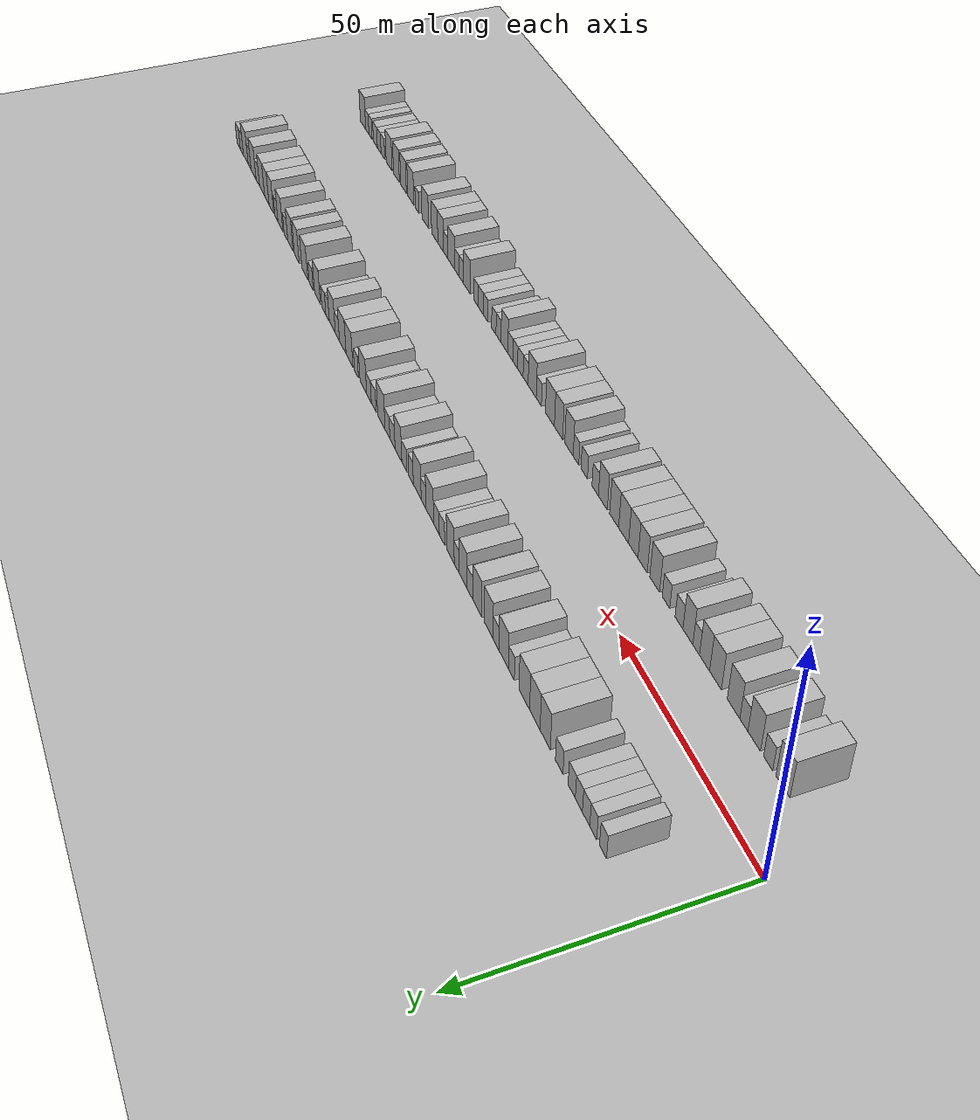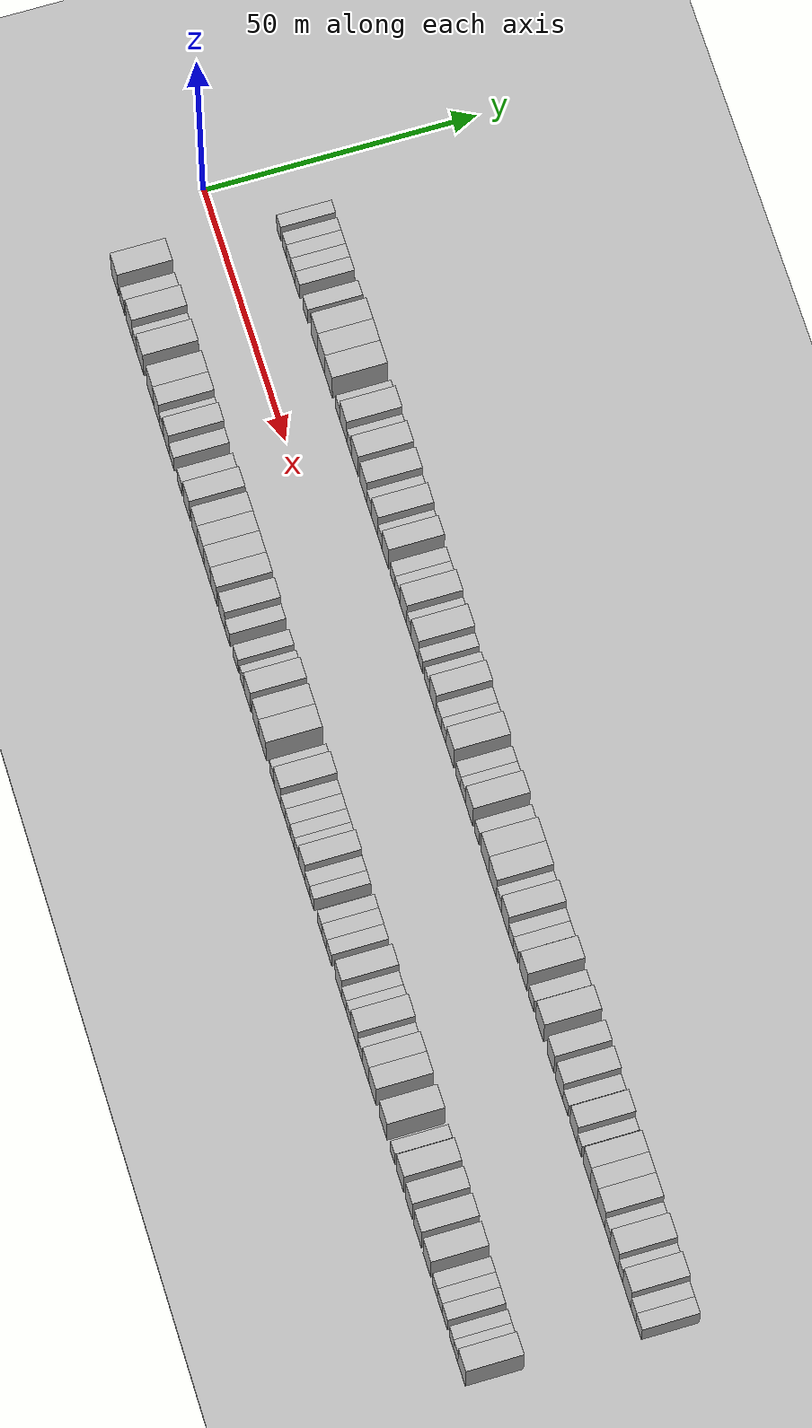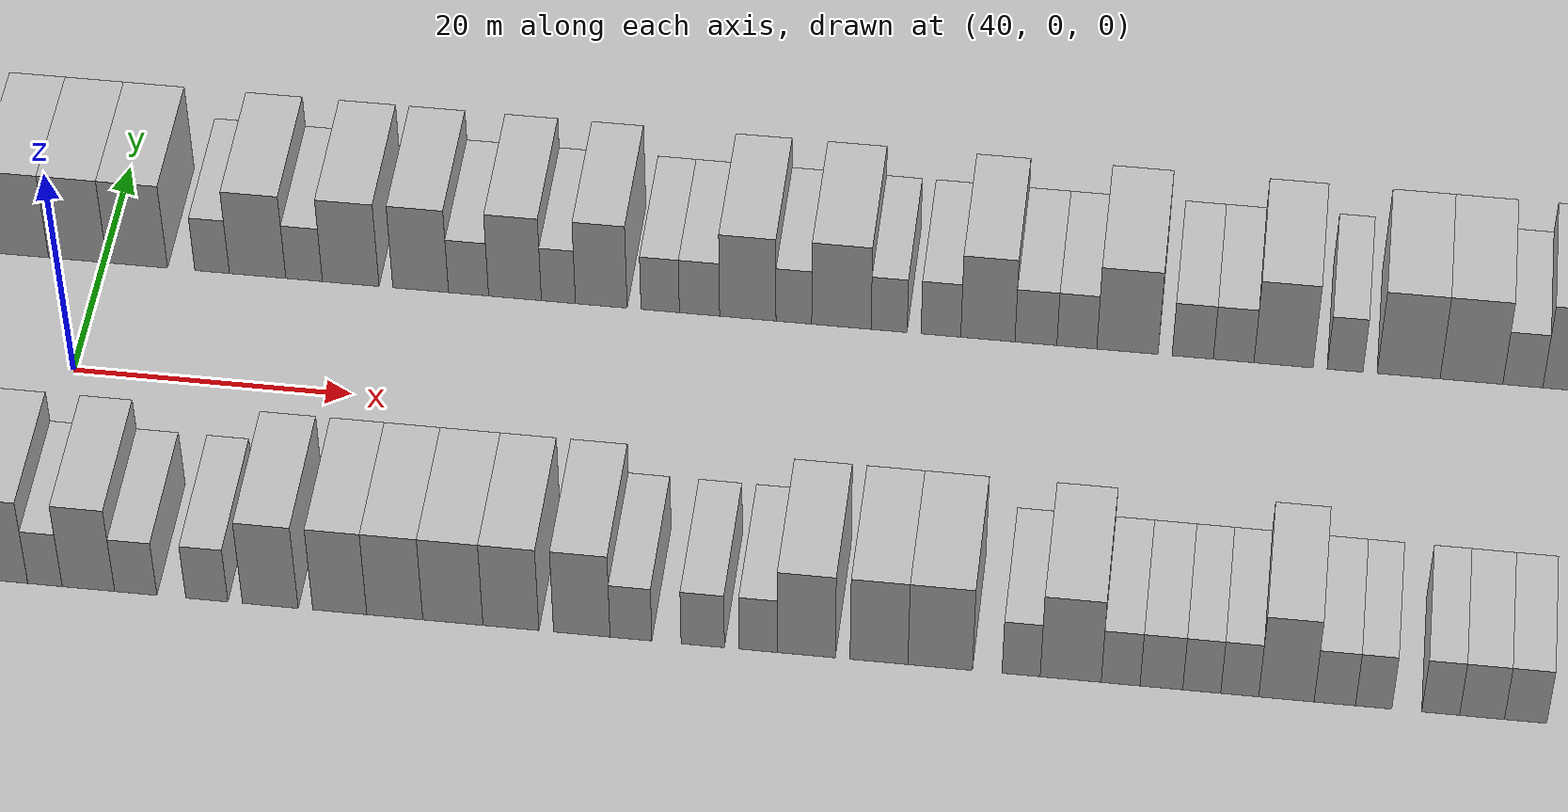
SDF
<?xml version="1.0" encoding="utf-8"?>

<sdf version="1.6">

   <world name="default">

      <gui fullscreen="0">

         <camera name="user_camera">

            <pose>-15 0 4.57585 0 0 0</pose>

            <view_controller>orbit</view_controller>

         </camera>

      </gui>

      <scene>

         <sky>

           <clouds>

             <speed>12</speed>

           </clouds>

         </sky>

         <ambient>0.4 0.4 0.4 1</ambient>

         <background>0.7 0.7 0.7 1</background>

         <shadows>1</shadows>

      </scene>

      <gravity>0 0 -9.8066</gravity>

      <magnetic_field>6e-06 2.3e-05 -4.2e-05</magnetic_field>

      <physics default="0" name="default_physics" type="ode">

         <ode>

            <solver>

               <type>quick</type>

               <iters>10</iters>

               <sor>1.0</sor>

               <use_dynamic_moi_rescaling>0</use_dynamic_moi_rescaling>

            </solver>

            <constraints>

               <cfm>0</cfm>

               <erp>0.2</erp>

               <contact_max_correcting_vel>100</contact_max_correcting_vel>

               <contact_surface_layer>0.001</contact_surface_layer>

            </constraints>

         </ode>

         <max_step_size>0.004</max_step_size>

         <real_time_factor>1</real_time_factor>

         <real_time_update_rate>250</real_time_update_rate>

      </physics>

      <light name="sun" type="directional">

         <cast_shadows>1</cast_shadows>

         <pose>0 0 10 0 0 0</pose>

         <diffuse>0.8 0.8 0.8 1</diffuse>

         <specular>0.2 0.2 0.2 1</specular>

         <attenuation>

            <range>1000</range>

            <constant>0.9</constant>

            <linear>0.01</linear>

            <quadratic>0.001</quadratic>

         </attenuation>

         <direction>-0.5 0.1 -0.9</direction>

      </light>

      <include>

         <name>ground_plane_1</name>

         <uri>model://HANNAS_ground_plane</uri>

         <pose>0 0 0  0 0 0</pose>

      </include>

      <include>

         <name>ground_plane_2</name>

         <uri>model://HANNAS_ground_plane</uri>

         <pose>100 0 0  0 0 0</pose>

      </include>

      <model name="building_1">

         <static>1</static>

         <pose frame="">12.2512 15.0000 0 0.000000 0.000000 1.570796</pose>

         <link name="link">

            <pose frame="">0 0 3.00 0 0 0</pose>

            <collision name="collision">

               <geometry>

                  <box>

                     <size>10.0000 2.5024 6.0000</size>

                  </box>

               </geometry>

               <max_contacts>10</max_contacts>

               <surface>

                  <contact>

                     <ode/>

                  </contact>

                  <bounce/>

                  <friction>

                     <torsional>

                        <ode/>

                     </torsional>

                     <ode/>

                  </friction>

               </surface>

            </collision>

            <visual name="visual">

               <cast_shadows>0</cast_shadows>

               <geometry>

                  <box>

                     <size>10.0000 2.5024 6.0000</size>

                  </box>

               </geometry>

               <material>

                  <script>

                     <uri>model://HANNAS_wall/materials/scripts</uri>

                     <uri>model://HANNAS_wall/materials/textures</uri>

                     <name>vrc/HANNAS_wall</name>

                  </script>

               </material>

            </visual>

            <self_collide>0</self_collide>

            <enable_wind>0</enable_wind>

            <kinematic>0</kinematic>

         </link>

      </model>

      <model name="building_2">

         <static>1</static>

         <pose frame="">15.7438 15.0000 0 0.000000 0.000000 1.570796</pose>

         <link name="link">

            <pose frame="">0 0 3.00 0 0 0</pose>

            <collision name="collision">

               <geometry>

                  <box>

                     <size>10.0000 2.4828 6.0000</size>

                  </box>

               </geometry>

               <max_contacts>10</max_contacts>

               <surface>

                  <contact>

                     <ode/>

                  </contact>

                  <bounce/>

                  <friction>

                     <torsional>

                        <ode/>

                     </torsional>

                     <ode/>

                  </friction>

               </surface>

            </collision>

            <visual name="visual">

               <cast_shadows>0</cast_shadows>

               <geometry>

                  <box>

                     <size>10.0000 2.4828 6.0000</size>

                  </box>

               </geometry>

               <material>

                  <script>

                     <uri>model://HANNAS_wall/materials/scripts</uri>

                     <uri>model://HANNAS_wall/materials/textures</uri>

                     <name>vrc/HANNAS_wall</name>

                  </script>

               </material>

            </visual>

            <self_collide>0</self_collide>

            <enable_wind>0</enable_wind>

            <kinematic>0</kinematic>

         </link>

      </model>

      <model name="building_3">

         <static>1</static>

         <pose frame="">18.3443 15.0000 0 0.000000 0.000000 1.570796</pose>

         <link name="link">

            <pose frame="">0 0 3.00 0 0 0</pose>

            <collision name="collision">

               <geometry>

                  <box>

                     <size>10.0000 2.7182 6.0000</size>

                  </box>

               </geometry>

               <max_contacts>10</max_contacts>

               <surface>

                  <contact>

                     <ode/>

                  </contact>

                  <bounce/>

                  <friction>

                     <torsional>

                        <ode/>

                     </torsional>

                     <ode/>

                  </friction>

               </surface>

            </collision>

            <visual name="visual">

               <cast_shadows>0</cast_shadows>

               <geometry>

                  <box>

                     <size>10.0000 2.7182 6.0000</size>

                  </box>

               </geometry>

               <material>

                  <script>

                     <uri>model://HANNAS_wall/materials/scripts</uri>

                     <uri>model://HANNAS_wall/materials/textures</uri>

                     <name>vrc/HANNAS_wall</name>

                  </script>

               </material>

            </visual>

            <self_collide>0</self_collide>

            <enable_wind>0</enable_wind>

            <kinematic>0</kinematic>

         </link>

      </model>

      <model name="building_4">

         <static>1</static>

         <pose frame="">21.0118 15.0000 0 0.000000 0.000000 1.570796</pose>

         <link name="link">

            <pose frame="">0 0 3.00 0 0 0</pose>

            <collision name="collision">

               <geometry>

                  <box>

                     <size>10.0000 2.6168 6.0000</size>

                  </box>

               </geometry>

               <max_contacts>10</max_contacts>

               <surface>

                  <contact>

                     <ode/>

                  </contact>

                  <bounce/>

                  <friction>

                     <torsional>

                        <ode/>

                     </torsional>

                     <ode/>

                  </friction>

               </surface>

            </collision>

            <visual name="visual">

               <cast_shadows>0</cast_shadows>

               <geometry>

                  <box>

                     <size>10.0000 2.6168 6.0000</size>

                  </box>

               </geometry>

               <material>

                  <script>

                     <uri>model://HANNAS_wall/materials/scripts</uri>

                     <uri>model://HANNAS_wall/materials/textures</uri>

                     <name>vrc/HANNAS_wall</name>

                  </script>

               </material>

            </visual>

            <self_collide>0</self_collide>

            <enable_wind>0</enable_wind>

            <kinematic>0</kinematic>

         </link>

      </model>

      <model name="building_5">

         <static>1</static>

         <pose frame="">23.6738 15.0000 0 0.000000 0.000000 1.570796</pose>

         <link name="link">

            <pose frame="">0 0 3.00 0 0 0</pose>

            <collision name="collision">

               <geometry>

                  <box>

                     <size>10.0000 2.7073 6.0000</size>

                  </box>

               </geometry>

               <max_contacts>10</max_contacts>

               <surface>

                  <contact>

                     <ode/>

                  </contact>

                  <bounce/>

                  <friction>

                     <torsional>

                        <ode/>

                     </torsional>

                     <ode/>

                  </friction>

               </surface>

            </collision>

            <visual name="visual">

               <cast_shadows>0</cast_shadows>

               <geometry>

                  <box>

                     <size>10.0000 2.7073 6.0000</size>

                  </box>

               </geometry>

               <material>

                  <script>

                     <uri>model://HANNAS_wall/materials/scripts</uri>

                     <uri>model://HANNAS_wall/materials/textures</uri>

                     <name>vrc/HANNAS_wall</name>

                  </script>

               </material>

            </visual>

            <self_collide>0</self_collide>

            <enable_wind>0</enable_wind>

            <kinematic>0</kinematic>

         </link>

      </model>

      <model name="building_6">

         <static>1</static>

         <pose frame="">28.4945 15.0000 0 0.000000 0.000000 1.570796</pose>

         <link name="link">

            <pose frame="">0 0 3.00 0 0 0</pose>

            <collision name="collision">

               <geometry>

                  <box>

                     <size>10.0000 2.9341 6.0000</size>

                  </box>

               </geometry>

               <max_contacts>10</max_contacts>

               <surface>

                  <contact>

                     <ode/>

                  </contact>

                  <bounce/>

                  <friction>

                     <torsional>

                        <ode/>

                     </torsional>

                     <ode/>

                  </friction>

               </surface>

            </collision>

            <visual name="visual">

               <cast_shadows>0</cast_shadows>

               <geometry>

                  <box>

                     <size>10.0000 2.9341 6.0000</size>

                  </box>

               </geometry>

               <material>

                  <script>

                     <uri>model://HANNAS_wall/materials/scripts</uri>

                     <uri>model://HANNAS_wall/materials/textures</uri>

                     <name>vrc/HANNAS_wall</name>

                  </script>

               </material>

            </visual>

            <self_collide>0</self_collide>

            <enable_wind>0</enable_wind>

            <kinematic>0</kinematic>

         </link>

      </model>

      <model name="building_7">

         <static>1</static>

         <pose frame="">34.0111 15.0000 0 0.000000 0.000000 1.570796</pose>

         <link name="link">

            <pose frame="">0 0 4.50 0 0 0</pose>

            <collision name="collision">

               <geometry>

                  <box>

                     <size>10.0000 4.0992 9.0000</size>

                  </box>

               </geometry>

               <max_contacts>10</max_contacts>

               <surface>

                  <contact>

                     <ode/>

                  </contact>

                  <bounce/>

                  <friction>

                     <torsional>

                        <ode/>

                     </torsional>

                     <ode/>

                  </friction>

               </surface>

            </collision>

            <visual name="visual">

               <cast_shadows>0</cast_shadows>

               <geometry>

                  <box>

                     <size>10.0000 4.0992 9.0000</size>

                  </box>

               </geometry>

               <material>

                  <script>

                     <uri>model://HANNAS_wall/materials/scripts</uri>

                     <uri>model://HANNAS_wall/materials/textures</uri>

                     <name>vrc/HANNAS_wall</name>

                  </script>

               </material>

            </visual>

            <self_collide>0</self_collide>

            <enable_wind>0</enable_wind>

            <kinematic>0</kinematic>

         </link>

      </model>

      <model name="building_8">

         <static>1</static>

         <pose frame="">38.2104 15.0000 0 0.000000 0.000000 1.570796</pose>

         <link name="link">

            <pose frame="">0 0 4.50 0 0 0</pose>

            <collision name="collision">

               <geometry>

                  <box>

                     <size>10.0000 4.2993 9.0000</size>

                  </box>

               </geometry>

               <max_contacts>10</max_contacts>

               <surface>

                  <contact>

                     <ode/>

                  </contact>

                  <bounce/>

                  <friction>

                     <torsional>

                        <ode/>

                     </torsional>

                     <ode/>

                  </friction>

               </surface>

            </collision>

            <visual name="visual">

               <cast_shadows>0</cast_shadows>

               <geometry>

                  <box>

                     <size>10.0000 4.2993 9.0000</size>

                  </box>

               </geometry>

               <material>

                  <script>

                     <uri>model://HANNAS_wall/materials/scripts</uri>

                     <uri>model://HANNAS_wall/materials/textures</uri>

                     <name>vrc/HANNAS_wall</name>

                  </script>

               </material>

            </visual>

            <self_collide>0</self_collide>

            <enable_wind>0</enable_wind>

            <kinematic>0</kinematic>

         </link>

      </model>

      <model name="building_9">

         <static>1</static>

         <pose frame="">42.5813 15.0000 0 0.000000 0.000000 1.570796</pose>

         <link name="link">

            <pose frame="">0 0 4.50 0 0 0</pose>

            <collision name="collision">

               <geometry>

                  <box>

                     <size>10.0000 4.4426 9.0000</size>

                  </box>

               </geometry>

               <max_contacts>10</max_contacts>

               <surface>

                  <contact>

                     <ode/>

                  </contact>

                  <bounce/>

                  <friction>

                     <torsional>

                        <ode/>

                     </torsional>

                     <ode/>

                  </friction>

               </surface>

            </collision>

            <visual name="visual">

               <cast_shadows>0</cast_shadows>

               <geometry>

                  <box>

                     <size>10.0000 4.4426 9.0000</size>

                  </box>

               </geometry>

               <material>

                  <script>

                     <uri>model://HANNAS_wall/materials/scripts</uri>

                     <uri>model://HANNAS_wall/materials/textures</uri>

                     <name>vrc/HANNAS_wall</name>

                  </script>

               </material>

            </visual>

            <self_collide>0</self_collide>

            <enable_wind>0</enable_wind>

            <kinematic>0</kinematic>

         </link>

      </model>

      <model name="building_10">

         <static>1</static>

         <pose frame="">48.0679 15.0000 0 0.000000 0.000000 1.570796</pose>

         <link name="link">

            <pose frame="">0 0 3.00 0 0 0</pose>

            <collision name="collision">

               <geometry>

                  <box>

                     <size>10.0000 2.5305 6.0000</size>

                  </box>

               </geometry>

               <max_contacts>10</max_contacts>

               <surface>

                  <contact>

                     <ode/>

                  </contact>

                  <bounce/>

                  <friction>

                     <torsional>

                        <ode/>

                     </torsional>

                     <ode/>

                  </friction>

               </surface>

            </collision>

            <visual name="visual">

               <cast_shadows>0</cast_shadows>

               <geometry>

                  <box>

                     <size>10.0000 2.5305 6.0000</size>

                  </box>

               </geometry>

               <material>

                  <script>

                     <uri>model://HANNAS_wall/materials/scripts</uri>

                     <uri>model://HANNAS_wall/materials/textures</uri>

                     <name>vrc/HANNAS_wall</name>

                  </script>

               </material>

            </visual>

            <self_collide>0</self_collide>

            <enable_wind>0</enable_wind>

            <kinematic>0</kinematic>

         </link>

      </model>

      <model name="building_11">

         <static>1</static>

         <pose frame="">51.3964 15.0000 0 0.000000 0.000000 1.570796</pose>

         <link name="link">

            <pose frame="">0 0 4.50 0 0 0</pose>

            <collision name="collision">

               <geometry>

                  <box>

                     <size>10.0000 4.1266 9.0000</size>

                  </box>

               </geometry>

               <max_contacts>10</max_contacts>

               <surface>

                  <contact>

                     <ode/>

                  </contact>

                  <bounce/>

                  <friction>

                     <torsional>

                        <ode/>

                     </torsional>

                     <ode/>

                  </friction>

               </surface>

            </collision>

            <visual name="visual">

               <cast_shadows>0</cast_shadows>

               <geometry>

                  <box>

                     <size>10.0000 4.1266 9.0000</size>

                  </box>

               </geometry>

               <material>

                  <script>

                     <uri>model://HANNAS_wall/materials/scripts</uri>

                     <uri>model://HANNAS_wall/materials/textures</uri>

                     <name>vrc/HANNAS_wall</name>

                  </script>

               </material>

            </visual>

            <self_collide>0</self_collide>

            <enable_wind>0</enable_wind>

            <kinematic>0</kinematic>

         </link>

      </model>

      <model name="building_12">

         <static>1</static>

         <pose frame="">54.7969 15.0000 0 0.000000 0.000000 1.570796</pose>

         <link name="link">

            <pose frame="">0 0 3.00 0 0 0</pose>

            <collision name="collision">

               <geometry>

                  <box>

                     <size>10.0000 2.6744 6.0000</size>

                  </box>

               </geometry>

               <max_contacts>10</max_contacts>

               <surface>

                  <contact>

                     <ode/>

                  </contact>

                  <bounce/>

                  <friction>

                     <torsional>

                        <ode/>

                     </torsional>

                     <ode/>

                  </friction>

               </surface>

            </collision>

            <visual name="visual">

               <cast_shadows>0</cast_shadows>

               <geometry>

                  <box>

                     <size>10.0000 2.6744 6.0000</size>

                  </box>

               </geometry>

               <material>

                  <script>

                     <uri>model://HANNAS_wall/materials/scripts</uri>

                     <uri>model://HANNAS_wall/materials/textures</uri>

                     <name>vrc/HANNAS_wall</name>

                  </script>

               </material>

            </visual>

            <self_collide>0</self_collide>

            <enable_wind>0</enable_wind>

            <kinematic>0</kinematic>

         </link>

      </model>

      <model name="building_13">

         <static>1</static>

         <pose frame="">58.2003 15.0000 0 0.000000 0.000000 1.570796</pose>

         <link name="link">

            <pose frame="">0 0 4.50 0 0 0</pose>

            <collision name="collision">

               <geometry>

                  <box>

                     <size>10.0000 4.1324 9.0000</size>

                  </box>

               </geometry>

               <max_contacts>10</max_contacts>

               <surface>

                  <contact>

                     <ode/>

                  </contact>

                  <bounce/>

                  <friction>

                     <torsional>

                        <ode/>

                     </torsional>

                     <ode/>

                  </friction>

               </surface>

            </collision>

            <visual name="visual">

               <cast_shadows>0</cast_shadows>

               <geometry>

                  <box>

                     <size>10.0000 4.1324 9.0000</size>

                  </box>

               </geometry>

               <material>

                  <script>

                     <uri>model://HANNAS_wall/materials/scripts</uri>

                     <uri>model://HANNAS_wall/materials/textures</uri>

                     <name>vrc/HANNAS_wall</name>

                  </script>

               </material>

            </visual>

            <self_collide>0</self_collide>

            <enable_wind>0</enable_wind>

            <kinematic>0</kinematic>

         </link>

      </model>

      <model name="building_14">

         <static>1</static>

         <pose frame="">63.2929 15.0000 0 0.000000 0.000000 1.570796</pose>

         <link name="link">

            <pose frame="">0 0 4.50 0 0 0</pose>

            <collision name="collision">

               <geometry>

                  <box>

                     <size>10.0000 4.0527 9.0000</size>

                  </box>

               </geometry>

               <max_contacts>10</max_contacts>

               <surface>

                  <contact>

                     <ode/>

                  </contact>

                  <bounce/>

                  <friction>

                     <torsional>

                        <ode/>

                     </torsional>

                     <ode/>

                  </friction>

               </surface>

            </collision>

            <visual name="visual">

               <cast_shadows>0</cast_shadows>

               <geometry>

                  <box>

                     <size>10.0000 4.0527 9.0000</size>

                  </box>

               </geometry>

               <material>

                  <script>

                     <uri>model://HANNAS_wall/materials/scripts</uri>

                     <uri>model://HANNAS_wall/materials/textures</uri>

                     <name>vrc/HANNAS_wall</name>

                  </script>

               </material>

            </visual>

            <self_collide>0</self_collide>

            <enable_wind>0</enable_wind>

            <kinematic>0</kinematic>

         </link>

      </model>

      <model name="building_15">

         <static>1</static>

         <pose frame="">66.7770 15.0000 0 0.000000 0.000000 1.570796</pose>

         <link name="link">

            <pose frame="">0 0 3.00 0 0 0</pose>

            <collision name="collision">

               <geometry>

                  <box>

                     <size>10.0000 2.9155 6.0000</size>

                  </box>

               </geometry>

               <max_contacts>10</max_contacts>

               <surface>

                  <contact>

                     <ode/>

                  </contact>

                  <bounce/>

                  <friction>

                     <torsional>

                        <ode/>

                     </torsional>

                     <ode/>

                  </friction>

               </surface>

            </collision>

            <visual name="visual">

               <cast_shadows>0</cast_shadows>

               <geometry>

                  <box>

                     <size>10.0000 2.9155 6.0000</size>

                  </box>

               </geometry>

               <material>

                  <script>

                     <uri>model://HANNAS_wall/materials/scripts</uri>

                     <uri>model://HANNAS_wall/materials/textures</uri>

                     <name>vrc/HANNAS_wall</name>

                  </script>

               </material>

            </visual>

            <self_collide>0</self_collide>

            <enable_wind>0</enable_wind>

            <kinematic>0</kinematic>

         </link>

      </model>

      <model name="building_16">

         <static>1</static>

         <pose frame="">70.1506 15.0000 0 0.000000 0.000000 1.570796</pose>

         <link name="link">

            <pose frame="">0 0 4.50 0 0 0</pose>

            <collision name="collision">

               <geometry>

                  <box>

                     <size>10.0000 3.8317 9.0000</size>

                  </box>

               </geometry>

               <max_contacts>10</max_contacts>

               <surface>

                  <contact>

                     <ode/>

                  </contact>

                  <bounce/>

                  <friction>

                     <torsional>

                        <ode/>

                     </torsional>

                     <ode/>

                  </friction>

               </surface>

            </collision>

            <visual name="visual">

               <cast_shadows>0</cast_shadows>

               <geometry>

                  <box>

                     <size>10.0000 3.8317 9.0000</size>

                  </box>

               </geometry>

               <material>

                  <script>

                     <uri>model://HANNAS_wall/materials/scripts</uri>

                     <uri>model://HANNAS_wall/materials/textures</uri>

                     <name>vrc/HANNAS_wall</name>

                  </script>

               </material>

            </visual>

            <self_collide>0</self_collide>

            <enable_wind>0</enable_wind>

            <kinematic>0</kinematic>

         </link>

      </model>

      <model name="building_17">

         <static>1</static>

         <pose frame="">73.3016 15.0000 0 0.000000 0.000000 1.570796</pose>

         <link name="link">

            <pose frame="">0 0 3.00 0 0 0</pose>

            <collision name="collision">

               <geometry>

                  <box>

                     <size>10.0000 2.4702 6.0000</size>

                  </box>

               </geometry>

               <max_contacts>10</max_contacts>

               <surface>

                  <contact>

                     <ode/>

                  </contact>

                  <bounce/>

                  <friction>

                     <torsional>

                        <ode/>

                     </torsional>

                     <ode/>

                  </friction>

               </surface>

            </collision>

            <visual name="visual">

               <cast_shadows>0</cast_shadows>

               <geometry>

                  <box>

                     <size>10.0000 2.4702 6.0000</size>

                  </box>

               </geometry>

               <material>

                  <script>

                     <uri>model://HANNAS_wall/materials/scripts</uri>

                     <uri>model://HANNAS_wall/materials/textures</uri>

                     <name>vrc/HANNAS_wall</name>

                  </script>

               </material>

            </visual>

            <self_collide>0</self_collide>

            <enable_wind>0</enable_wind>

            <kinematic>0</kinematic>

         </link>

      </model>

      <model name="building_18">

         <static>1</static>

         <pose frame="">76.4071 15.0000 0 0.000000 0.000000 1.570796</pose>

         <link name="link">

            <pose frame="">0 0 4.50 0 0 0</pose>

            <collision name="collision">

               <geometry>

                  <box>

                     <size>10.0000 3.7410 9.0000</size>

                  </box>

               </geometry>

               <max_contacts>10</max_contacts>

               <surface>

                  <contact>

                     <ode/>

                  </contact>

                  <bounce/>

                  <friction>

                     <torsional>

                        <ode/>

                     </torsional>

                     <ode/>

                  </friction>

               </surface>

            </collision>

            <visual name="visual">

               <cast_shadows>0</cast_shadows>

               <geometry>

                  <box>

                     <size>10.0000 3.7410 9.0000</size>

                  </box>

               </geometry>

               <material>

                  <script>

                     <uri>model://HANNAS_wall/materials/scripts</uri>

                     <uri>model://HANNAS_wall/materials/textures</uri>

                     <name>vrc/HANNAS_wall</name>

                  </script>

               </material>

            </visual>

            <self_collide>0</self_collide>

            <enable_wind>0</enable_wind>

            <kinematic>0</kinematic>

         </link>

      </model>

      <model name="building_19">

         <static>1</static>

         <pose frame="">80.6656 15.0000 0 0.000000 0.000000 1.570796</pose>

         <link name="link">

            <pose frame="">0 0 3.00 0 0 0</pose>

            <collision name="collision">

               <geometry>

                  <box>

                     <size>10.0000 2.7760 6.0000</size>

                  </box>

               </geometry>

               <max_contacts>10</max_contacts>

               <surface>

                  <contact>

                     <ode/>

                  </contact>

                  <bounce/>

                  <friction>

                     <torsional>

                        <ode/>

                     </torsional>

                     <ode/>

                  </friction>

               </surface>

            </collision>

            <visual name="visual">

               <cast_shadows>0</cast_shadows>

               <geometry>

                  <box>

                     <size>10.0000 2.7760 6.0000</size>

                  </box>

               </geometry>

               <material>

                  <script>

                     <uri>model://HANNAS_wall/materials/scripts</uri>

                     <uri>model://HANNAS_wall/materials/textures</uri>

                     <name>vrc/HANNAS_wall</name>

                  </script>

               </material>

            </visual>

            <self_collide>0</self_collide>

            <enable_wind>0</enable_wind>

            <kinematic>0</kinematic>

         </link>

      </model>

      <model name="building_20">

         <static>1</static>

         <pose frame="">83.5055 15.0000 0 0.000000 0.000000 1.570796</pose>

         <link name="link">

            <pose frame="">0 0 3.00 0 0 0</pose>

            <collision name="collision">

               <geometry>

                  <box>

                     <size>10.0000 2.9038 6.0000</size>

                  </box>

               </geometry>

               <max_contacts>10</max_contacts>

               <surface>

                  <contact>

                     <ode/>

                  </contact>

                  <bounce/>

                  <friction>

                     <torsional>

                        <ode/>

                     </torsional>

                     <ode/>

                  </friction>

               </surface>

            </collision>

            <visual name="visual">

               <cast_shadows>0</cast_shadows>

               <geometry>

                  <box>

                     <size>10.0000 2.9038 6.0000</size>

                  </box>

               </geometry>

               <material>

                  <script>

                     <uri>model://HANNAS_wall/materials/scripts</uri>

                     <uri>model://HANNAS_wall/materials/textures</uri>

                     <name>vrc/HANNAS_wall</name>

                  </script>

               </material>

            </visual>

            <self_collide>0</self_collide>

            <enable_wind>0</enable_wind>

            <kinematic>0</kinematic>

         </link>

      </model>

      <model name="building_21">

         <static>1</static>

         <pose frame="">86.9885 15.0000 0 0.000000 0.000000 1.570796</pose>

         <link name="link">

            <pose frame="">0 0 4.50 0 0 0</pose>

            <collision name="collision">

               <geometry>

                  <box>

                     <size>10.0000 4.0622 9.0000</size>

                  </box>

               </geometry>

               <max_contacts>10</max_contacts>

               <surface>

                  <contact>

                     <ode/>

                  </contact>

                  <bounce/>

                  <friction>

                     <torsional>

                        <ode/>

                     </torsional>

                     <ode/>

                  </friction>

               </surface>

            </collision>

            <visual name="visual">

               <cast_shadows>0</cast_shadows>

               <geometry>

                  <box>

                     <size>10.0000 4.0622 9.0000</size>

                  </box>

               </geometry>

               <material>

                  <script>

                     <uri>model://HANNAS_wall/materials/scripts</uri>

                     <uri>model://HANNAS_wall/materials/textures</uri>

                     <name>vrc/HANNAS_wall</name>

                  </script>

               </material>

            </visual>

            <self_collide>0</self_collide>

            <enable_wind>0</enable_wind>

            <kinematic>0</kinematic>

         </link>

      </model>

      <model name="building_22">

         <static>1</static>

         <pose frame="">90.3040 15.0000 0 0.000000 0.000000 1.570796</pose>

         <link name="link">

            <pose frame="">0 0 3.00 0 0 0</pose>

            <collision name="collision">

               <geometry>

                  <box>

                     <size>10.0000 2.5687 6.0000</size>

                  </box>

               </geometry>

               <max_contacts>10</max_contacts>

               <surface>

                  <contact>

                     <ode/>

                  </contact>

                  <bounce/>

                  <friction>

                     <torsional>

                        <ode/>

                     </torsional>

                     <ode/>

                  </friction>

               </surface>

            </collision>

            <visual name="visual">

               <cast_shadows>0</cast_shadows>

               <geometry>

                  <box>

                     <size>10.0000 2.5687 6.0000</size>

                  </box>

               </geometry>

               <material>

                  <script>

                     <uri>model://HANNAS_wall/materials/scripts</uri>

                     <uri>model://HANNAS_wall/materials/textures</uri>

                     <name>vrc/HANNAS_wall</name>

                  </script>

               </material>

            </visual>

            <self_collide>0</self_collide>

            <enable_wind>0</enable_wind>

            <kinematic>0</kinematic>

         </link>

      </model>

      <model name="building_23">

         <static>1</static>

         <pose frame="">93.7211 15.0000 0 0.000000 0.000000 1.570796</pose>

         <link name="link">

            <pose frame="">0 0 4.50 0 0 0</pose>

            <collision name="collision">

               <geometry>

                  <box>

                     <size>10.0000 4.2655 9.0000</size>

                  </box>

               </geometry>

               <max_contacts>10</max_contacts>

               <surface>

                  <contact>

                     <ode/>

                  </contact>

                  <bounce/>

                  <friction>

                     <torsional>

                        <ode/>

                     </torsional>

                     <ode/>

                  </friction>

               </surface>

            </collision>

            <visual name="visual">

               <cast_shadows>0</cast_shadows>

               <geometry>

                  <box>

                     <size>10.0000 4.2655 9.0000</size>

                  </box>

               </geometry>

               <material>

                  <script>

                     <uri>model://HANNAS_wall/materials/scripts</uri>

                     <uri>model://HANNAS_wall/materials/textures</uri>

                     <name>vrc/HANNAS_wall</name>

                  </script>

               </material>

            </visual>

            <self_collide>0</self_collide>

            <enable_wind>0</enable_wind>

            <kinematic>0</kinematic>

         </link>

      </model>

      <model name="building_24">

         <static>1</static>

         <pose frame="">97.1481 15.0000 0 0.000000 0.000000 1.570796</pose>

         <link name="link">

            <pose frame="">0 0 3.00 0 0 0</pose>

            <collision name="collision">

               <geometry>

                  <box>

                     <size>10.0000 2.5886 6.0000</size>

                  </box>

               </geometry>

               <max_contacts>10</max_contacts>

               <surface>

                  <contact>

                     <ode/>

                  </contact>

                  <bounce/>

                  <friction>

                     <torsional>

                        <ode/>

                     </torsional>

                     <ode/>

                  </friction>

               </surface>

            </collision>

            <visual name="visual">

               <cast_shadows>0</cast_shadows>

               <geometry>

                  <box>

                     <size>10.0000 2.5886 6.0000</size>

                  </box>

               </geometry>

               <material>

                  <script>

                     <uri>model://HANNAS_wall/materials/scripts</uri>

                     <uri>model://HANNAS_wall/materials/textures</uri>

                     <name>vrc/HANNAS_wall</name>

                  </script>

               </material>

            </visual>

            <self_collide>0</self_collide>

            <enable_wind>0</enable_wind>

            <kinematic>0</kinematic>

         </link>

      </model>

      <model name="building_25">

         <static>1</static>

         <pose frame="">100.8649 15.0000 0 0.000000 0.000000 1.570796</pose>

         <link name="link">

            <pose frame="">0 0 3.00 0 0 0</pose>

            <collision name="collision">

               <geometry>

                  <box>

                     <size>10.0000 2.8450 6.0000</size>

                  </box>

               </geometry>

               <max_contacts>10</max_contacts>

               <surface>

                  <contact>

                     <ode/>

                  </contact>

                  <bounce/>

                  <friction>

                     <torsional>

                        <ode/>

                     </torsional>

                     <ode/>

                  </friction>

               </surface>

            </collision>

            <visual name="visual">

               <cast_shadows>0</cast_shadows>

               <geometry>

                  <box>

                     <size>10.0000 2.8450 6.0000</size>

                  </box>

               </geometry>

               <material>

                  <script>

                     <uri>model://HANNAS_wall/materials/scripts</uri>

                     <uri>model://HANNAS_wall/materials/textures</uri>

                     <name>vrc/HANNAS_wall</name>

                  </script>

               </material>

            </visual>

            <self_collide>0</self_collide>

            <enable_wind>0</enable_wind>

            <kinematic>0</kinematic>

         </link>

      </model>

      <model name="building_26">

         <static>1</static>

         <pose frame="">104.2250 15.0000 0 0.000000 0.000000 1.570796</pose>

         <link name="link">

            <pose frame="">0 0 4.50 0 0 0</pose>

            <collision name="collision">

               <geometry>

                  <box>

                     <size>10.0000 3.8752 9.0000</size>

                  </box>

               </geometry>

               <max_contacts>10</max_contacts>

               <surface>

                  <contact>

                     <ode/>

                  </contact>

                  <bounce/>

                  <friction>

                     <torsional>

                        <ode/>

                     </torsional>

                     <ode/>

                  </friction>

               </surface>

            </collision>

            <visual name="visual">

               <cast_shadows>0</cast_shadows>

               <geometry>

                  <box>

                     <size>10.0000 3.8752 9.0000</size>

                  </box>

               </geometry>

               <material>

                  <script>

                     <uri>model://HANNAS_wall/materials/scripts</uri>

                     <uri>model://HANNAS_wall/materials/textures</uri>

                     <name>vrc/HANNAS_wall</name>

                  </script>

               </material>

            </visual>

            <self_collide>0</self_collide>

            <enable_wind>0</enable_wind>

            <kinematic>0</kinematic>

         </link>

      </model>

      <model name="building_27">

         <static>1</static>

         <pose frame="">107.6613 15.0000 0 0.000000 0.000000 1.570796</pose>

         <link name="link">

            <pose frame="">0 0 3.00 0 0 0</pose>

            <collision name="collision">

               <geometry>

                  <box>

                     <size>10.0000 2.9974 6.0000</size>

                  </box>

               </geometry>

               <max_contacts>10</max_contacts>

               <surface>

                  <contact>

                     <ode/>

                  </contact>

                  <bounce/>

                  <friction>

                     <torsional>

                        <ode/>

                     </torsional>

                     <ode/>

                  </friction>

               </surface>

            </collision>

            <visual name="visual">

               <cast_shadows>0</cast_shadows>

               <geometry>

                  <box>

                     <size>10.0000 2.9974 6.0000</size>

                  </box>

               </geometry>

               <material>

                  <script>

                     <uri>model://HANNAS_wall/materials/scripts</uri>

                     <uri>model://HANNAS_wall/materials/textures</uri>

                     <name>vrc/HANNAS_wall</name>

                  </script>

               </material>

            </visual>

            <self_collide>0</self_collide>

            <enable_wind>0</enable_wind>

            <kinematic>0</kinematic>

         </link>

      </model>

      <model name="building_28">

         <static>1</static>

         <pose frame="">110.5838 15.0000 0 0.000000 0.000000 1.570796</pose>

         <link name="link">

            <pose frame="">0 0 3.00 0 0 0</pose>

            <collision name="collision">

               <geometry>

                  <box>

                     <size>10.0000 2.8476 6.0000</size>

                  </box>

               </geometry>

               <max_contacts>10</max_contacts>

               <surface>

                  <contact>

                     <ode/>

                  </contact>

                  <bounce/>

                  <friction>

                     <torsional>

                        <ode/>

                     </torsional>

                     <ode/>

                  </friction>

               </surface>

            </collision>

            <visual name="visual">

               <cast_shadows>0</cast_shadows>

               <geometry>

                  <box>

                     <size>10.0000 2.8476 6.0000</size>

                  </box>

               </geometry>

               <material>

                  <script>

                     <uri>model://HANNAS_wall/materials/scripts</uri>

                     <uri>model://HANNAS_wall/materials/textures</uri>

                     <name>vrc/HANNAS_wall</name>

                  </script>

               </material>

            </visual>

            <self_collide>0</self_collide>

            <enable_wind>0</enable_wind>

            <kinematic>0</kinematic>

         </link>

      </model>

      <model name="building_29">

         <static>1</static>

         <pose frame="">114.1921 15.0000 0 0.000000 0.000000 1.570796</pose>

         <link name="link">

            <pose frame="">0 0 4.50 0 0 0</pose>

            <collision name="collision">

               <geometry>

                  <box>

                     <size>10.0000 4.3690 9.0000</size>

                  </box>

               </geometry>

               <max_contacts>10</max_contacts>

               <surface>

                  <contact>

                     <ode/>

                  </contact>

                  <bounce/>

                  <friction>

                     <torsional>

                        <ode/>

                     </torsional>

                     <ode/>

                  </friction>

               </surface>

            </collision>

            <visual name="visual">

               <cast_shadows>0</cast_shadows>

               <geometry>

                  <box>

                     <size>10.0000 4.3690 9.0000</size>

                  </box>

               </geometry>

               <material>

                  <script>

                     <uri>model://HANNAS_wall/materials/scripts</uri>

                     <uri>model://HANNAS_wall/materials/textures</uri>

                     <name>vrc/HANNAS_wall</name>

                  </script>

               </material>

            </visual>

            <self_collide>0</self_collide>

            <enable_wind>0</enable_wind>

            <kinematic>0</kinematic>

         </link>

      </model>

      <model name="building_30">

         <static>1</static>

         <pose frame="">118.8395 15.0000 0 0.000000 0.000000 1.570796</pose>

         <link name="link">

            <pose frame="">0 0 3.00 0 0 0</pose>

            <collision name="collision">

               <geometry>

                  <box>

                     <size>10.0000 2.9260 6.0000</size>

                  </box>

               </geometry>

               <max_contacts>10</max_contacts>

               <surface>

                  <contact>

                     <ode/>

                  </contact>

                  <bounce/>

                  <friction>

                     <torsional>

                        <ode/>

                     </torsional>

                     <ode/>

                  </friction>

               </surface>

            </collision>

            <visual name="visual">

               <cast_shadows>0</cast_shadows>

               <geometry>

                  <box>

                     <size>10.0000 2.9260 6.0000</size>

                  </box>

               </geometry>

               <material>

                  <script>

                     <uri>model://HANNAS_wall/materials/scripts</uri>

                     <uri>model://HANNAS_wall/materials/textures</uri>

                     <name>vrc/HANNAS_wall</name>

                  </script>

               </material>

            </visual>

            <self_collide>0</self_collide>

            <enable_wind>0</enable_wind>

            <kinematic>0</kinematic>

         </link>

      </model>

      <model name="building_31">

         <static>1</static>

         <pose frame="">121.7471 15.0000 0 0.000000 0.000000 1.570796</pose>

         <link name="link">

            <pose frame="">0 0 3.00 0 0 0</pose>

            <collision name="collision">

               <geometry>

                  <box>

                     <size>10.0000 2.8892 6.0000</size>

                  </box>

               </geometry>

               <max_contacts>10</max_contacts>

               <surface>

                  <contact>

                     <ode/>

                  </contact>

                  <bounce/>

                  <friction>

                     <torsional>

                        <ode/>

                     </torsional>

                     <ode/>

                  </friction>

               </surface>

            </collision>

            <visual name="visual">

               <cast_shadows>0</cast_shadows>

               <geometry>

                  <box>

                     <size>10.0000 2.8892 6.0000</size>

                  </box>

               </geometry>

               <material>

                  <script>

                     <uri>model://HANNAS_wall/materials/scripts</uri>

                     <uri>model://HANNAS_wall/materials/textures</uri>

                     <name>vrc/HANNAS_wall</name>

                  </script>

               </material>

            </visual>

            <self_collide>0</self_collide>

            <enable_wind>0</enable_wind>

            <kinematic>0</kinematic>

         </link>

      </model>

      <model name="building_32">

         <static>1</static>

         <pose frame="">125.2870 15.0000 0 0.000000 0.000000 1.570796</pose>

         <link name="link">

            <pose frame="">0 0 4.50 0 0 0</pose>

            <collision name="collision">

               <geometry>

                  <box>

                     <size>10.0000 4.1906 9.0000</size>

                  </box>

               </geometry>

               <max_contacts>10</max_contacts>

               <surface>

                  <contact>

                     <ode/>

                  </contact>

                  <bounce/>

                  <friction>

                     <torsional>

                        <ode/>

                     </torsional>

                     <ode/>

                  </friction>

               </surface>

            </collision>

            <visual name="visual">

               <cast_shadows>0</cast_shadows>

               <geometry>

                  <box>

                     <size>10.0000 4.1906 9.0000</size>

                  </box>

               </geometry>

               <material>

                  <script>

                     <uri>model://HANNAS_wall/materials/scripts</uri>

                     <uri>model://HANNAS_wall/materials/textures</uri>

                     <name>vrc/HANNAS_wall</name>

                  </script>

               </material>

            </visual>

            <self_collide>0</self_collide>

            <enable_wind>0</enable_wind>

            <kinematic>0</kinematic>

         </link>

      </model>

      <model name="building_33">

         <static>1</static>

         <pose frame="">129.6487 15.0000 0 0.000000 0.000000 1.570796</pose>

         <link name="link">

            <pose frame="">0 0 3.00 0 0 0</pose>

            <collision name="collision">

               <geometry>

                  <box>

                     <size>10.0000 2.5326 6.0000</size>

                  </box>

               </geometry>

               <max_contacts>10</max_contacts>

               <surface>

                  <contact>

                     <ode/>

                  </contact>

                  <bounce/>

                  <friction>

                     <torsional>

                        <ode/>

                     </torsional>

                     <ode/>

                  </friction>

               </surface>

            </collision>

            <visual name="visual">

               <cast_shadows>0</cast_shadows>

               <geometry>

                  <box>

                     <size>10.0000 2.5326 6.0000</size>

                  </box>

               </geometry>

               <material>

                  <script>

                     <uri>model://HANNAS_wall/materials/scripts</uri>

                     <uri>model://HANNAS_wall/materials/textures</uri>

                     <name>vrc/HANNAS_wall</name>

                  </script>

               </material>

            </visual>

            <self_collide>0</self_collide>

            <enable_wind>0</enable_wind>

            <kinematic>0</kinematic>

         </link>

      </model>

      <model name="building_34">

         <static>1</static>

         <pose frame="">134.1399 15.0000 0 0.000000 0.000000 1.570796</pose>

         <link name="link">

            <pose frame="">0 0 4.50 0 0 0</pose>

            <collision name="collision">

               <geometry>

                  <box>

                     <size>10.0000 4.4499 9.0000</size>

                  </box>

               </geometry>

               <max_contacts>10</max_contacts>

               <surface>

                  <contact>

                     <ode/>

                  </contact>

                  <bounce/>

                  <friction>

                     <torsional>

                        <ode/>

                     </torsional>

                     <ode/>

                  </friction>

               </surface>

            </collision>

            <visual name="visual">

               <cast_shadows>0</cast_shadows>

               <geometry>

                  <box>

                     <size>10.0000 4.4499 9.0000</size>

                  </box>

               </geometry>

               <material>

                  <script>

                     <uri>model://HANNAS_wall/materials/scripts</uri>

                     <uri>model://HANNAS_wall/materials/textures</uri>

                     <name>vrc/HANNAS_wall</name>

                  </script>

               </material>

            </visual>

            <self_collide>0</self_collide>

            <enable_wind>0</enable_wind>

            <kinematic>0</kinematic>

         </link>

      </model>

      <model name="building_35">

         <static>1</static>

         <pose frame="">138.5769 15.0000 0 0.000000 0.000000 1.570796</pose>

         <link name="link">

            <pose frame="">0 0 4.50 0 0 0</pose>

            <collision name="collision">

               <geometry>

                  <box>

                     <size>10.0000 4.4240 9.0000</size>

                  </box>

               </geometry>

               <max_contacts>10</max_contacts>

               <surface>

                  <contact>

                     <ode/>

                  </contact>

                  <bounce/>

                  <friction>

                     <torsional>

                        <ode/>

                     </torsional>

                     <ode/>

                  </friction>

               </surface>

            </collision>

            <visual name="visual">

               <cast_shadows>0</cast_shadows>

               <geometry>

                  <box>

                     <size>10.0000 4.4240 9.0000</size>

                  </box>

               </geometry>

               <material>

                  <script>

                     <uri>model://HANNAS_wall/materials/scripts</uri>

                     <uri>model://HANNAS_wall/materials/textures</uri>

                     <name>vrc/HANNAS_wall</name>

                  </script>

               </material>

            </visual>

            <self_collide>0</self_collide>

            <enable_wind>0</enable_wind>

            <kinematic>0</kinematic>

         </link>

      </model>

      <model name="building_36">

         <static>1</static>

         <pose frame="">142.1965 15.0000 0 0.000000 0.000000 1.570796</pose>

         <link name="link">

            <pose frame="">0 0 3.00 0 0 0</pose>

            <collision name="collision">

               <geometry>

                  <box>

                     <size>10.0000 2.8153 6.0000</size>

                  </box>

               </geometry>

               <max_contacts>10</max_contacts>

               <surface>

                  <contact>

                     <ode/>

                  </contact>

                  <bounce/>

                  <friction>

                     <torsional>

                        <ode/>

                     </torsional>

                     <ode/>

                  </friction>

               </surface>

            </collision>

            <visual name="visual">

               <cast_shadows>0</cast_shadows>

               <geometry>

                  <box>

                     <size>10.0000 2.8153 6.0000</size>

                  </box>

               </geometry>

               <material>

                  <script>

                     <uri>model://HANNAS_wall/materials/scripts</uri>

                     <uri>model://HANNAS_wall/materials/textures</uri>

                     <name>vrc/HANNAS_wall</name>

                  </script>

               </material>

            </visual>

            <self_collide>0</self_collide>

            <enable_wind>0</enable_wind>

            <kinematic>0</kinematic>

         </link>

      </model>

      <model name="building_37">

         <static>1</static>

         <pose frame="">145.6440 15.0000 0 0.000000 0.000000 1.570796</pose>

         <link name="link">

            <pose frame="">0 0 4.50 0 0 0</pose>

            <collision name="collision">

               <geometry>

                  <box>

                     <size>10.0000 4.0796 9.0000</size>

                  </box>

               </geometry>

               <max_contacts>10</max_contacts>

               <surface>

                  <contact>

                     <ode/>

                  </contact>

                  <bounce/>

                  <friction>

                     <torsional>

                        <ode/>

                     </torsional>

                     <ode/>

                  </friction>

               </surface>

            </collision>

            <visual name="visual">

               <cast_shadows>0</cast_shadows>

               <geometry>

                  <box>

                     <size>10.0000 4.0796 9.0000</size>

                  </box>

               </geometry>

               <material>

                  <script>

                     <uri>model://HANNAS_wall/materials/scripts</uri>

                     <uri>model://HANNAS_wall/materials/textures</uri>

                     <name>vrc/HANNAS_wall</name>

                  </script>

               </material>

            </visual>

            <self_collide>0</self_collide>

            <enable_wind>0</enable_wind>

            <kinematic>0</kinematic>

         </link>

      </model>

      <model name="building_38">

         <static>1</static>

         <pose frame="">148.9304 15.0000 0 0.000000 0.000000 1.570796</pose>

         <link name="link">

            <pose frame="">0 0 3.00 0 0 0</pose>

            <collision name="collision">

               <geometry>

                  <box>

                     <size>10.0000 2.4932 6.0000</size>

                  </box>

               </geometry>

               <max_contacts>10</max_contacts>

               <surface>

                  <contact>

                     <ode/>

                  </contact>

                  <bounce/>

                  <friction>

                     <torsional>

                        <ode/>

                     </torsional>

                     <ode/>

                  </friction>

               </surface>

            </collision>

            <visual name="visual">

               <cast_shadows>0</cast_shadows>

               <geometry>

                  <box>

                     <size>10.0000 2.4932 6.0000</size>

                  </box>

               </geometry>

               <material>

                  <script>

                     <uri>model://HANNAS_wall/materials/scripts</uri>

                     <uri>model://HANNAS_wall/materials/textures</uri>

                     <name>vrc/HANNAS_wall</name>

                  </script>

               </material>

            </visual>

            <self_collide>0</self_collide>

            <enable_wind>0</enable_wind>

            <kinematic>0</kinematic>

         </link>

      </model>

      <model name="building_39">

         <static>1</static>

         <pose frame="">151.5765 15.0000 0 0.000000 0.000000 1.570796</pose>

         <link name="link">

            <pose frame="">0 0 3.00 0 0 0</pose>

            <collision name="collision">

               <geometry>

                  <box>

                     <size>10.0000 2.7991 6.0000</size>

                  </box>

               </geometry>

               <max_contacts>10</max_contacts>

               <surface>

                  <contact>

                     <ode/>

                  </contact>

                  <bounce/>

                  <friction>

                     <torsional>

                        <ode/>

                     </torsional>

                     <ode/>

                  </friction>

               </surface>

            </collision>

            <visual name="visual">

               <cast_shadows>0</cast_shadows>

               <geometry>

                  <box>

                     <size>10.0000 2.7991 6.0000</size>

                  </box>

               </geometry>

               <material>

                  <script>

                     <uri>model://HANNAS_wall/materials/scripts</uri>

                     <uri>model://HANNAS_wall/materials/textures</uri>

                     <name>vrc/HANNAS_wall</name>

                  </script>

               </material>

            </visual>

            <self_collide>0</self_collide>

            <enable_wind>0</enable_wind>

            <kinematic>0</kinematic>

         </link>

      </model>

      <model name="building_40">

         <static>1</static>

         <pose frame="">156.0516 15.0000 0 0.000000 0.000000 1.570796</pose>

         <link name="link">

            <pose frame="">0 0 4.50 0 0 0</pose>

            <collision name="collision">

               <geometry>

                  <box>

                     <size>10.0000 4.1510 9.0000</size>

                  </box>

               </geometry>

               <max_contacts>10</max_contacts>

               <surface>

                  <contact>

                     <ode/>

                  </contact>

                  <bounce/>

                  <friction>

                     <torsional>

                        <ode/>

                     </torsional>

                     <ode/>

                  </friction>

               </surface>

            </collision>

            <visual name="visual">

               <cast_shadows>0</cast_shadows>

               <geometry>

                  <box>

                     <size>10.0000 4.1510 9.0000</size>

                  </box>

               </geometry>

               <material>

                  <script>

                     <uri>model://HANNAS_wall/materials/scripts</uri>

                     <uri>model://HANNAS_wall/materials/textures</uri>

                     <name>vrc/HANNAS_wall</name>

                  </script>

               </material>

            </visual>

            <self_collide>0</self_collide>

            <enable_wind>0</enable_wind>

            <kinematic>0</kinematic>

         </link>

      </model>

      <model name="building_41">

         <static>1</static>

         <pose frame="">160.5889 15.0000 0 0.000000 0.000000 1.570796</pose>

         <link name="link">

            <pose frame="">0 0 3.00 0 0 0</pose>

            <collision name="collision">

               <geometry>

                  <box>

                     <size>10.0000 2.9237 6.0000</size>

                  </box>

               </geometry>

               <max_contacts>10</max_contacts>

               <surface>

                  <contact>

                     <ode/>

                  </contact>

                  <bounce/>

                  <friction>

                     <torsional>

                        <ode/>

                     </torsional>

                     <ode/>

                  </friction>

               </surface>

            </collision>

            <visual name="visual">

               <cast_shadows>0</cast_shadows>

               <geometry>

                  <box>

                     <size>10.0000 2.9237 6.0000</size>

                  </box>

               </geometry>

               <material>

                  <script>

                     <uri>model://HANNAS_wall/materials/scripts</uri>

                     <uri>model://HANNAS_wall/materials/textures</uri>

                     <name>vrc/HANNAS_wall</name>

                  </script>

               </material>

            </visual>

            <self_collide>0</self_collide>

            <enable_wind>0</enable_wind>

            <kinematic>0</kinematic>

         </link>

      </model>

      <model name="building_42">

         <static>1</static>

         <pose frame="">165.2645 15.0000 0 0.000000 0.000000 1.570796</pose>

         <link name="link">

            <pose frame="">0 0 4.50 0 0 0</pose>

            <collision name="collision">

               <geometry>

                  <box>

                     <size>10.0000 4.4274 9.0000</size>

                  </box>

               </geometry>

               <max_contacts>10</max_contacts>

               <surface>

                  <contact>

                     <ode/>

                  </contact>

                  <bounce/>

                  <friction>

                     <torsional>

                        <ode/>

                     </torsional>

                     <ode/>

                  </friction>

               </surface>

            </collision>

            <visual name="visual">

               <cast_shadows>0</cast_shadows>

               <geometry>

                  <box>

                     <size>10.0000 4.4274 9.0000</size>

                  </box>

               </geometry>

               <material>

                  <script>

                     <uri>model://HANNAS_wall/materials/scripts</uri>

                     <uri>model://HANNAS_wall/materials/textures</uri>

                     <name>vrc/HANNAS_wall</name>

                  </script>

               </material>

            </visual>

            <self_collide>0</self_collide>

            <enable_wind>0</enable_wind>

            <kinematic>0</kinematic>

         </link>

      </model>

      <model name="building_43">

         <static>1</static>

         <pose frame="">171.3550 15.0000 0 0.000000 0.000000 1.570796</pose>

         <link name="link">

            <pose frame="">0 0 4.50 0 0 0</pose>

            <collision name="collision">

               <geometry>

                  <box>

                     <size>10.0000 3.7536 9.0000</size>

                  </box>

               </geometry>

               <max_contacts>10</max_contacts>

               <surface>

                  <contact>

                     <ode/>

                  </contact>

                  <bounce/>

                  <friction>

                     <torsional>

                        <ode/>

                     </torsional>

                     <ode/>

                  </friction>

               </surface>

            </collision>

            <visual name="visual">

               <cast_shadows>0</cast_shadows>

               <geometry>

                  <box>

                     <size>10.0000 3.7536 9.0000</size>

                  </box>

               </geometry>

               <material>

                  <script>

                     <uri>model://HANNAS_wall/materials/scripts</uri>

                     <uri>model://HANNAS_wall/materials/textures</uri>

                     <name>vrc/HANNAS_wall</name>

                  </script>

               </material>

            </visual>

            <self_collide>0</self_collide>

            <enable_wind>0</enable_wind>

            <kinematic>0</kinematic>

         </link>

      </model>

      <model name="building_44">

         <static>1</static>

         <pose frame="">176.2489 15.0000 0 0.000000 0.000000 1.570796</pose>

         <link name="link">

            <pose frame="">0 0 4.50 0 0 0</pose>

            <collision name="collision">

               <geometry>

                  <box>

                     <size>10.0000 4.0343 9.0000</size>

                  </box>

               </geometry>

               <max_contacts>10</max_contacts>

               <surface>

                  <contact>

                     <ode/>

                  </contact>

                  <bounce/>

                  <friction>

                     <torsional>

                        <ode/>

                     </torsional>

                     <ode/>

                  </friction>

               </surface>

            </collision>

            <visual name="visual">

               <cast_shadows>0</cast_shadows>

               <geometry>

                  <box>

                     <size>10.0000 4.0343 9.0000</size>

                  </box>

               </geometry>

               <material>

                  <script>

                     <uri>model://HANNAS_wall/materials/scripts</uri>

                     <uri>model://HANNAS_wall/materials/textures</uri>

                     <name>vrc/HANNAS_wall</name>

                  </script>

               </material>

            </visual>

            <self_collide>0</self_collide>

            <enable_wind>0</enable_wind>

            <kinematic>0</kinematic>

         </link>

      </model>

      <model name="building_45">

         <static>1</static>

         <pose frame="">179.7240 15.0000 0 0.000000 0.000000 1.570796</pose>

         <link name="link">

            <pose frame="">0 0 3.00 0 0 0</pose>

            <collision name="collision">

               <geometry>

                  <box>

                     <size>10.0000 2.9158 6.0000</size>

                  </box>

               </geometry>

               <max_contacts>10</max_contacts>

               <surface>

                  <contact>

                     <ode/>

                  </contact>

                  <bounce/>

                  <friction>

                     <torsional>

                        <ode/>

                     </torsional>

                     <ode/>

                  </friction>

               </surface>

            </collision>

            <visual name="visual">

               <cast_shadows>0</cast_shadows>

               <geometry>

                  <box>

                     <size>10.0000 2.9158 6.0000</size>

                  </box>

               </geometry>

               <material>

                  <script>

                     <uri>model://HANNAS_wall/materials/scripts</uri>

                     <uri>model://HANNAS_wall/materials/textures</uri>

                     <name>vrc/HANNAS_wall</name>

                  </script>

               </material>

            </visual>

            <self_collide>0</self_collide>

            <enable_wind>0</enable_wind>

            <kinematic>0</kinematic>

         </link>

      </model>

      <model name="building_46">

         <static>1</static>

         <pose frame="">184.1755 15.0000 0 0.000000 0.000000 1.570796</pose>

         <link name="link">

            <pose frame="">0 0 4.50 0 0 0</pose>

            <collision name="collision">

               <geometry>

                  <box>

                     <size>10.0000 3.9871 9.0000</size>

                  </box>

               </geometry>

               <max_contacts>10</max_contacts>

               <surface>

                  <contact>

                     <ode/>

                  </contact>

                  <bounce/>

                  <friction>

                     <torsional>

                        <ode/>

                     </torsional>

                     <ode/>

                  </friction>

               </surface>

            </collision>

            <visual name="visual">

               <cast_shadows>0</cast_shadows>

               <geometry>

                  <box>

                     <size>10.0000 3.9871 9.0000</size>

                  </box>

               </geometry>

               <material>

                  <script>

                     <uri>model://HANNAS_wall/materials/scripts</uri>

                     <uri>model://HANNAS_wall/materials/textures</uri>

                     <name>vrc/HANNAS_wall</name>

                  </script>

               </material>

            </visual>

            <self_collide>0</self_collide>

            <enable_wind>0</enable_wind>

            <kinematic>0</kinematic>

         </link>

      </model>

      <model name="building_47">

         <static>1</static>

         <pose frame="">187.3735 15.0000 0 0.000000 0.000000 1.570796</pose>

         <link name="link">

            <pose frame="">0 0 3.00 0 0 0</pose>

            <collision name="collision">

               <geometry>

                  <box>

                     <size>10.0000 2.4090 6.0000</size>

                  </box>

               </geometry>

               <max_contacts>10</max_contacts>

               <surface>

                  <contact>

                     <ode/>

                  </contact>

                  <bounce/>

                  <friction>

                     <torsional>

                        <ode/>

                     </torsional>

                     <ode/>

                  </friction>

               </surface>

            </collision>

            <visual name="visual">

               <cast_shadows>0</cast_shadows>

               <geometry>

                  <box>

                     <size>10.0000 2.4090 6.0000</size>

                  </box>

               </geometry>

               <material>

                  <script>

                     <uri>model://HANNAS_wall/materials/scripts</uri>

                     <uri>model://HANNAS_wall/materials/textures</uri>

                     <name>vrc/HANNAS_wall</name>

                  </script>

               </material>

            </visual>

            <self_collide>0</self_collide>

            <enable_wind>0</enable_wind>

            <kinematic>0</kinematic>

         </link>

      </model>

      <model name="building_48">

         <static>1</static>

         <pose frame="">191.5131 15.0000 0 0.000000 0.000000 1.570796</pose>

         <link name="link">

            <pose frame="">0 0 4.50 0 0 0</pose>

            <collision name="collision">

               <geometry>

                  <box>

                     <size>10.0000 3.8702 9.0000</size>

                  </box>

               </geometry>

               <max_contacts>10</max_contacts>

               <surface>

                  <contact>

                     <ode/>

                  </contact>

                  <bounce/>

                  <friction>

                     <torsional>

                        <ode/>

                     </torsional>

                     <ode/>

                  </friction>

               </surface>

            </collision>

            <visual name="visual">

               <cast_shadows>0</cast_shadows>

               <geometry>

                  <box>

                     <size>10.0000 3.8702 9.0000</size>

                  </box>

               </geometry>

               <material>

                  <script>

                     <uri>model://HANNAS_wall/materials/scripts</uri>

                     <uri>model://HANNAS_wall/materials/textures</uri>

                     <name>vrc/HANNAS_wall</name>

                  </script>

               </material>

            </visual>

            <self_collide>0</self_collide>

            <enable_wind>0</enable_wind>

            <kinematic>0</kinematic>

         </link>

      </model>

      <model name="building_49">

         <static>1</static>

         <pose frame="">195.3071 15.0000 0 0.000000 0.000000 1.570796</pose>

         <link name="link">

            <pose frame="">0 0 4.50 0 0 0</pose>

            <collision name="collision">

               <geometry>

                  <box>

                     <size>10.0000 3.7177 9.0000</size>

                  </box>

               </geometry>

               <max_contacts>10</max_contacts>

               <surface>

                  <contact>

                     <ode/>

                  </contact>

                  <bounce/>

                  <friction>

                     <torsional>

                        <ode/>

                     </torsional>

                     <ode/>

                  </friction>

               </surface>

            </collision>

            <visual name="visual">

               <cast_shadows>0</cast_shadows>

               <geometry>

                  <box>

                     <size>10.0000 3.7177 9.0000</size>

                  </box>

               </geometry>

               <material>

                  <script>

                     <uri>model://HANNAS_wall/materials/scripts</uri>

                     <uri>model://HANNAS_wall/materials/textures</uri>

                     <name>vrc/HANNAS_wall</name>

                  </script>

               </material>

            </visual>

            <self_collide>0</self_collide>

            <enable_wind>0</enable_wind>

            <kinematic>0</kinematic>

         </link>

      </model>

      <model name="building_50">

         <static>1</static>

         <pose frame="">199.3210 15.0000 0 0.000000 0.000000 1.570796</pose>

         <link name="link">

            <pose frame="">0 0 4.50 0 0 0</pose>

            <collision name="collision">

               <geometry>

                  <box>

                     <size>10.0000 4.3102 9.0000</size>

                  </box>

               </geometry>

               <max_contacts>10</max_contacts>

               <surface>

                  <contact>

                     <ode/>

                  </contact>

                  <bounce/>

                  <friction>

                     <torsional>

                        <ode/>

                     </torsional>

                     <ode/>

                  </friction>

               </surface>

            </collision>

            <visual name="visual">

               <cast_shadows>0</cast_shadows>

               <geometry>

                  <box>

                     <size>10.0000 4.3102 9.0000</size>

                  </box>

               </geometry>

               <material>

                  <script>

                     <uri>model://HANNAS_wall/materials/scripts</uri>

                     <uri>model://HANNAS_wall/materials/textures</uri>

                     <name>vrc/HANNAS_wall</name>

                  </script>

               </material>

            </visual>

            <self_collide>0</self_collide>

            <enable_wind>0</enable_wind>

            <kinematic>0</kinematic>

         </link>

      </model>

      <model name="building_51">

         <static>1</static>

         <pose frame="">202.9413 15.0000 0 0.000000 0.000000 1.570796</pose>

         <link name="link">

            <pose frame="">0 0 3.00 0 0 0</pose>

            <collision name="collision">

               <geometry>

                  <box>

                     <size>10.0000 2.9304 6.0000</size>

                  </box>

               </geometry>

               <max_contacts>10</max_contacts>

               <surface>

                  <contact>

                     <ode/>

                  </contact>

                  <bounce/>

                  <friction>

                     <torsional>

                        <ode/>

                     </torsional>

                     <ode/>

                  </friction>

               </surface>

            </collision>

            <visual name="visual">

               <cast_shadows>0</cast_shadows>

               <geometry>

                  <box>

                     <size>10.0000 2.9304 6.0000</size>

                  </box>

               </geometry>

               <material>

                  <script>

                     <uri>model://HANNAS_wall/materials/scripts</uri>

                     <uri>model://HANNAS_wall/materials/textures</uri>

                     <name>vrc/HANNAS_wall</name>

                  </script>

               </material>

            </visual>

            <self_collide>0</self_collide>

            <enable_wind>0</enable_wind>

            <kinematic>0</kinematic>

         </link>

      </model>

      <model name="building_52">

         <static>1</static>

         <pose frame="">206.6378 15.0000 0 0.000000 0.000000 1.570796</pose>

         <link name="link">

            <pose frame="">0 0 4.50 0 0 0</pose>

            <collision name="collision">

               <geometry>

                  <box>

                     <size>10.0000 4.4625 9.0000</size>

                  </box>

               </geometry>

               <max_contacts>10</max_contacts>

               <surface>

                  <contact>

                     <ode/>

                  </contact>

                  <bounce/>

                  <friction>

                     <torsional>

                        <ode/>

                     </torsional>

                     <ode/>

                  </friction>

               </surface>

            </collision>

            <visual name="visual">

               <cast_shadows>0</cast_shadows>

               <geometry>

                  <box>

                     <size>10.0000 4.4625 9.0000</size>

                  </box>

               </geometry>

               <material>

                  <script>

                     <uri>model://HANNAS_wall/materials/scripts</uri>

                     <uri>model://HANNAS_wall/materials/textures</uri>

                     <name>vrc/HANNAS_wall</name>

                  </script>

               </material>

            </visual>

            <self_collide>0</self_collide>

            <enable_wind>0</enable_wind>

            <kinematic>0</kinematic>

         </link>

      </model>

      <model name="building_53">

         <static>1</static>

         <pose frame="">210.1238 15.0000 0 0.000000 0.000000 1.570796</pose>

         <link name="link">

            <pose frame="">0 0 3.00 0 0 0</pose>

            <collision name="collision">

               <geometry>

                  <box>

                     <size>10.0000 2.5096 6.0000</size>

                  </box>

               </geometry>

               <max_contacts>10</max_contacts>

               <surface>

                  <contact>

                     <ode/>

                  </contact>

                  <bounce/>

                  <friction>

                     <torsional>

                        <ode/>

                     </torsional>

                     <ode/>

                  </friction>

               </surface>

            </collision>

            <visual name="visual">

               <cast_shadows>0</cast_shadows>

               <geometry>

                  <box>

                     <size>10.0000 2.5096 6.0000</size>

                  </box>

               </geometry>

               <material>

                  <script>

                     <uri>model://HANNAS_wall/materials/scripts</uri>

                     <uri>model://HANNAS_wall/materials/textures</uri>

                     <name>vrc/HANNAS_wall</name>

                  </script>

               </material>

            </visual>

            <self_collide>0</self_collide>

            <enable_wind>0</enable_wind>

            <kinematic>0</kinematic>

         </link>

      </model>

      <model name="building_54">

         <static>1</static>

         <pose frame="">213.5482 15.0000 0 0.000000 0.000000 1.570796</pose>

         <link name="link">

            <pose frame="">0 0 4.50 0 0 0</pose>

            <collision name="collision">

               <geometry>

                  <box>

                     <size>10.0000 4.3391 9.0000</size>

                  </box>

               </geometry>

               <max_contacts>10</max_contacts>

               <surface>

                  <contact>

                     <ode/>

                  </contact>

                  <bounce/>

                  <friction>

                     <torsional>

                        <ode/>

                     </torsional>

                     <ode/>

                  </friction>

               </surface>

            </collision>

            <visual name="visual">

               <cast_shadows>0</cast_shadows>

               <geometry>

                  <box>

                     <size>10.0000 4.3391 9.0000</size>

                  </box>

               </geometry>

               <material>

                  <script>

                     <uri>model://HANNAS_wall/materials/scripts</uri>

                     <uri>model://HANNAS_wall/materials/textures</uri>

                     <name>vrc/HANNAS_wall</name>

                  </script>

               </material>

            </visual>

            <self_collide>0</self_collide>

            <enable_wind>0</enable_wind>

            <kinematic>0</kinematic>

         </link>

      </model>

      <model name="building_55">

         <static>1</static>

         <pose frame="">217.0966 15.0000 0 0.000000 0.000000 1.570796</pose>

         <link name="link">

            <pose frame="">0 0 3.00 0 0 0</pose>

            <collision name="collision">

               <geometry>

                  <box>

                     <size>10.0000 2.7576 6.0000</size>

                  </box>

               </geometry>

               <max_contacts>10</max_contacts>

               <surface>

                  <contact>

                     <ode/>

                  </contact>

                  <bounce/>

                  <friction>

                     <torsional>

                        <ode/>

                     </torsional>

                     <ode/>

                  </friction>

               </surface>

            </collision>

            <visual name="visual">

               <cast_shadows>0</cast_shadows>

               <geometry>

                  <box>

                     <size>10.0000 2.7576 6.0000</size>

                  </box>

               </geometry>

               <material>

                  <script>

                     <uri>model://HANNAS_wall/materials/scripts</uri>

                     <uri>model://HANNAS_wall/materials/textures</uri>

                     <name>vrc/HANNAS_wall</name>

                  </script>

               </material>

            </visual>

            <self_collide>0</self_collide>

            <enable_wind>0</enable_wind>

            <kinematic>0</kinematic>

         </link>

      </model>

      <model name="building_56">

         <static>1</static>

         <pose frame="">219.9685 15.0000 0 0.000000 0.000000 1.570796</pose>

         <link name="link">

            <pose frame="">0 0 3.00 0 0 0</pose>

            <collision name="collision">

               <geometry>

                  <box>

                     <size>10.0000 2.9861 6.0000</size>

                  </box>

               </geometry>

               <max_contacts>10</max_contacts>

               <surface>

                  <contact>

                     <ode/>

                  </contact>

                  <bounce/>

                  <friction>

                     <torsional>

                        <ode/>

                     </torsional>

                     <ode/>

                  </friction>

               </surface>

            </collision>

            <visual name="visual">

               <cast_shadows>0</cast_shadows>

               <geometry>

                  <box>

                     <size>10.0000 2.9861 6.0000</size>

                  </box>

               </geometry>

               <material>

                  <script>

                     <uri>model://HANNAS_wall/materials/scripts</uri>

                     <uri>model://HANNAS_wall/materials/textures</uri>

                     <name>vrc/HANNAS_wall</name>

                  </script>

               </material>

            </visual>

            <self_collide>0</self_collide>

            <enable_wind>0</enable_wind>

            <kinematic>0</kinematic>

         </link>

      </model>

      <model name="building_57">

         <static>1</static>

         <pose frame="">13.1892 -15.0000 0 0.000000 0.000000 1.570796</pose>

         <link name="link">

            <pose frame="">0 0 4.50 0 0 0</pose>

            <collision name="collision">

               <geometry>

                  <box>

                     <size>10.0000 4.3785 9.0000</size>

                  </box>

               </geometry>

               <max_contacts>10</max_contacts>

               <surface>

                  <contact>

                     <ode/>

                  </contact>

                  <bounce/>

                  <friction>

                     <torsional>

                        <ode/>

                     </torsional>

                     <ode/>

                  </friction>

               </surface>

            </collision>

            <visual name="visual">

               <cast_shadows>0</cast_shadows>

               <geometry>

                  <box>

                     <size>10.0000 4.3785 9.0000</size>

                  </box>

               </geometry>

               <material>

                  <script>

                     <uri>model://HANNAS_wall/materials/scripts</uri>

                     <uri>model://HANNAS_wall/materials/textures</uri>

                     <name>vrc/HANNAS_wall</name>

                  </script>

               </material>

            </visual>

            <self_collide>0</self_collide>

            <enable_wind>0</enable_wind>

            <kinematic>0</kinematic>

         </link>

      </model>

      <model name="building_58">

         <static>1</static>

         <pose frame="">17.8253 -15.0000 0 0.000000 0.000000 1.570796</pose>

         <link name="link">

            <pose frame="">0 0 3.00 0 0 0</pose>

            <collision name="collision">

               <geometry>

                  <box>

                     <size>10.0000 2.8936 6.0000</size>

                  </box>

               </geometry>

               <max_contacts>10</max_contacts>

               <surface>

                  <contact>

                     <ode/>

                  </contact>

                  <bounce/>

                  <friction>

                     <torsional>

                        <ode/>

                     </torsional>

                     <ode/>

                  </friction>

               </surface>

            </collision>

            <visual name="visual">

               <cast_shadows>0</cast_shadows>

               <geometry>

                  <box>

                     <size>10.0000 2.8936 6.0000</size>

                  </box>

               </geometry>

               <material>

                  <script>

                     <uri>model://HANNAS_wall/materials/scripts</uri>

                     <uri>model://HANNAS_wall/materials/textures</uri>

                     <name>vrc/HANNAS_wall</name>

                  </script>

               </material>

            </visual>

            <self_collide>0</self_collide>

            <enable_wind>0</enable_wind>

            <kinematic>0</kinematic>

         </link>

      </model>

      <model name="building_59">

         <static>1</static>

         <pose frame="">22.3184 -15.0000 0 0.000000 0.000000 1.570796</pose>

         <link name="link">

            <pose frame="">0 0 4.50 0 0 0</pose>

            <collision name="collision">

               <geometry>

                  <box>

                     <size>10.0000 4.0927 9.0000</size>

                  </box>

               </geometry>

               <max_contacts>10</max_contacts>

               <surface>

                  <contact>

                     <ode/>

                  </contact>

                  <bounce/>

                  <friction>

                     <torsional>

                        <ode/>

                     </torsional>

                     <ode/>

                  </friction>

               </surface>

            </collision>

            <visual name="visual">

               <cast_shadows>0</cast_shadows>

               <geometry>

                  <box>

                     <size>10.0000 4.0927 9.0000</size>

                  </box>

               </geometry>

               <material>

                  <script>

                     <uri>model://HANNAS_wall/materials/scripts</uri>

                     <uri>model://HANNAS_wall/materials/textures</uri>

                     <name>vrc/HANNAS_wall</name>

                  </script>

               </material>

            </visual>

            <self_collide>0</self_collide>

            <enable_wind>0</enable_wind>

            <kinematic>0</kinematic>

         </link>

      </model>

      <model name="building_60">

         <static>1</static>

         <pose frame="">25.7051 -15.0000 0 0.000000 0.000000 1.570796</pose>

         <link name="link">

            <pose frame="">0 0 3.00 0 0 0</pose>

            <collision name="collision">

               <geometry>

                  <box>

                     <size>10.0000 2.6806 6.0000</size>

                  </box>

               </geometry>

               <max_contacts>10</max_contacts>

               <surface>

                  <contact>

                     <ode/>

                  </contact>

                  <bounce/>

                  <friction>

                     <torsional>

                        <ode/>

                     </torsional>

                     <ode/>

                  </friction>

               </surface>

            </collision>

            <visual name="visual">

               <cast_shadows>0</cast_shadows>

               <geometry>

                  <box>

                     <size>10.0000 2.6806 6.0000</size>

                  </box>

               </geometry>

               <material>

                  <script>

                     <uri>model://HANNAS_wall/materials/scripts</uri>

                     <uri>model://HANNAS_wall/materials/textures</uri>

                     <name>vrc/HANNAS_wall</name>

                  </script>

               </material>

            </visual>

            <self_collide>0</self_collide>

            <enable_wind>0</enable_wind>

            <kinematic>0</kinematic>

         </link>

      </model>

      <model name="building_61">

         <static>1</static>

         <pose frame="">29.1625 -15.0000 0 0.000000 0.000000 1.570796</pose>

         <link name="link">

            <pose frame="">0 0 4.50 0 0 0</pose>

            <collision name="collision">

               <geometry>

                  <box>

                     <size>10.0000 4.2343 9.0000</size>

                  </box>

               </geometry>

               <max_contacts>10</max_contacts>

               <surface>

                  <contact>

                     <ode/>

                  </contact>

                  <bounce/>

                  <friction>

                     <torsional>

                        <ode/>

                     </torsional>

                     <ode/>

                  </friction>

               </surface>

            </collision>

            <visual name="visual">

               <cast_shadows>0</cast_shadows>

               <geometry>

                  <box>

                     <size>10.0000 4.2343 9.0000</size>

                  </box>

               </geometry>

               <material>

                  <script>

                     <uri>model://HANNAS_wall/materials/scripts</uri>

                     <uri>model://HANNAS_wall/materials/textures</uri>

                     <name>vrc/HANNAS_wall</name>

                  </script>

               </material>

            </visual>

            <self_collide>0</self_collide>

            <enable_wind>0</enable_wind>

            <kinematic>0</kinematic>

         </link>

      </model>

      <model name="building_62">

         <static>1</static>

         <pose frame="">35.3511 -15.0000 0 0.000000 0.000000 1.570796</pose>

         <link name="link">

            <pose frame="">0 0 4.50 0 0 0</pose>

            <collision name="collision">

               <geometry>

                  <box>

                     <size>10.0000 4.1427 9.0000</size>

                  </box>

               </geometry>

               <max_contacts>10</max_contacts>

               <surface>

                  <contact>

                     <ode/>

                  </contact>

                  <bounce/>

                  <friction>

                     <torsional>

                        <ode/>

                     </torsional>

                     <ode/>

                  </friction>

               </surface>

            </collision>

            <visual name="visual">

               <cast_shadows>0</cast_shadows>

               <geometry>

                  <box>

                     <size>10.0000 4.1427 9.0000</size>

                  </box>

               </geometry>

               <material>

                  <script>

                     <uri>model://HANNAS_wall/materials/scripts</uri>

                     <uri>model://HANNAS_wall/materials/textures</uri>

                     <name>vrc/HANNAS_wall</name>

                  </script>

               </material>

            </visual>

            <self_collide>0</self_collide>

            <enable_wind>0</enable_wind>

            <kinematic>0</kinematic>

         </link>

      </model>

      <model name="building_63">

         <static>1</static>

         <pose frame="">39.2301 -15.0000 0 0.000000 0.000000 1.570796</pose>

         <link name="link">

            <pose frame="">0 0 4.50 0 0 0</pose>

            <collision name="collision">

               <geometry>

                  <box>

                     <size>10.0000 3.6155 9.0000</size>

                  </box>

               </geometry>

               <max_contacts>10</max_contacts>

               <surface>

                  <contact>

                     <ode/>

                  </contact>

                  <bounce/>

                  <friction>

                     <torsional>

                        <ode/>

                     </torsional>

                     <ode/>

                  </friction>

               </surface>

            </collision>

            <visual name="visual">

               <cast_shadows>0</cast_shadows>

               <geometry>

                  <box>

                     <size>10.0000 3.6155 9.0000</size>

                  </box>

               </geometry>

               <material>

                  <script>

                     <uri>model://HANNAS_wall/materials/scripts</uri>

                     <uri>model://HANNAS_wall/materials/textures</uri>

                     <name>vrc/HANNAS_wall</name>

                  </script>

               </material>

            </visual>

            <self_collide>0</self_collide>

            <enable_wind>0</enable_wind>

            <kinematic>0</kinematic>

         </link>

      </model>

      <model name="building_64">

         <static>1</static>

         <pose frame="">42.2406 -15.0000 0 0.000000 0.000000 1.570796</pose>

         <link name="link">

            <pose frame="">0 0 3.00 0 0 0</pose>

            <collision name="collision">

               <geometry>

                  <box>

                     <size>10.0000 2.4054 6.0000</size>

                  </box>

               </geometry>

               <max_contacts>10</max_contacts>

               <surface>

                  <contact>

                     <ode/>

                  </contact>

                  <bounce/>

                  <friction>

                     <torsional>

                        <ode/>

                     </torsional>

                     <ode/>

                  </friction>

               </surface>

            </collision>

            <visual name="visual">

               <cast_shadows>0</cast_shadows>

               <geometry>

                  <box>

                     <size>10.0000 2.4054 6.0000</size>

                  </box>

               </geometry>

               <material>

                  <script>

                     <uri>model://HANNAS_wall/materials/scripts</uri>

                     <uri>model://HANNAS_wall/materials/textures</uri>

                     <name>vrc/HANNAS_wall</name>

                  </script>

               </material>

            </visual>

            <self_collide>0</self_collide>

            <enable_wind>0</enable_wind>

            <kinematic>0</kinematic>

         </link>

      </model>

      <model name="building_65">

         <static>1</static>

         <pose frame="">45.2627 -15.0000 0 0.000000 0.000000 1.570796</pose>

         <link name="link">

            <pose frame="">0 0 4.50 0 0 0</pose>

            <collision name="collision">

               <geometry>

                  <box>

                     <size>10.0000 3.6388 9.0000</size>

                  </box>

               </geometry>

               <max_contacts>10</max_contacts>

               <surface>

                  <contact>

                     <ode/>

                  </contact>

                  <bounce/>

                  <friction>

                     <torsional>

                        <ode/>

                     </torsional>

                     <ode/>

                  </friction>

               </surface>

            </collision>

            <visual name="visual">

               <cast_shadows>0</cast_shadows>

               <geometry>

                  <box>

                     <size>10.0000 3.6388 9.0000</size>

                  </box>

               </geometry>

               <material>

                  <script>

                     <uri>model://HANNAS_wall/materials/scripts</uri>

                     <uri>model://HANNAS_wall/materials/textures</uri>

                     <name>vrc/HANNAS_wall</name>

                  </script>

               </material>

            </visual>

            <self_collide>0</self_collide>

            <enable_wind>0</enable_wind>

            <kinematic>0</kinematic>

         </link>

      </model>

      <model name="building_66">

         <static>1</static>

         <pose frame="">48.5496 -15.0000 0 0.000000 0.000000 1.570796</pose>

         <link name="link">

            <pose frame="">0 0 3.00 0 0 0</pose>

            <collision name="collision">

               <geometry>

                  <box>

                     <size>10.0000 2.9351 6.0000</size>

                  </box>

               </geometry>

               <max_contacts>10</max_contacts>

               <surface>

                  <contact>

                     <ode/>

                  </contact>

                  <bounce/>

                  <friction>

                     <torsional>

                        <ode/>

                     </torsional>

                     <ode/>

                  </friction>

               </surface>

            </collision>

            <visual name="visual">

               <cast_shadows>0</cast_shadows>

               <geometry>

                  <box>

                     <size>10.0000 2.9351 6.0000</size>

                  </box>

               </geometry>

               <material>

                  <script>

                     <uri>model://HANNAS_wall/materials/scripts</uri>

                     <uri>model://HANNAS_wall/materials/textures</uri>

                     <name>vrc/HANNAS_wall</name>

                  </script>

               </material>

            </visual>

            <self_collide>0</self_collide>

            <enable_wind>0</enable_wind>

            <kinematic>0</kinematic>

         </link>

      </model>

      <model name="building_67">

         <static>1</static>

         <pose frame="">53.4762 -15.0000 0 0.000000 0.000000 1.570796</pose>

         <link name="link">

            <pose frame="">0 0 3.00 0 0 0</pose>

            <collision name="collision">

               <geometry>

                  <box>

                     <size>10.0000 2.9179 6.0000</size>

                  </box>

               </geometry>

               <max_contacts>10</max_contacts>

               <surface>

                  <contact>

                     <ode/>

                  </contact>

                  <bounce/>

                  <friction>

                     <torsional>

                        <ode/>

                     </torsional>

                     <ode/>

                  </friction>

               </surface>

            </collision>

            <visual name="visual">

               <cast_shadows>0</cast_shadows>

               <geometry>

                  <box>

                     <size>10.0000 2.9179 6.0000</size>

                  </box>

               </geometry>

               <material>

                  <script>

                     <uri>model://HANNAS_wall/materials/scripts</uri>

                     <uri>model://HANNAS_wall/materials/textures</uri>

                     <name>vrc/HANNAS_wall</name>

                  </script>

               </material>

            </visual>

            <self_collide>0</self_collide>

            <enable_wind>0</enable_wind>

            <kinematic>0</kinematic>

         </link>

      </model>

      <model name="building_68">

         <static>1</static>

         <pose frame="">57.8662 -15.0000 0 0.000000 0.000000 1.570796</pose>

         <link name="link">

            <pose frame="">0 0 4.50 0 0 0</pose>

            <collision name="collision">

               <geometry>

                  <box>

                     <size>10.0000 3.8623 9.0000</size>

                  </box>

               </geometry>

               <max_contacts>10</max_contacts>

               <surface>

                  <contact>

                     <ode/>

                  </contact>

                  <bounce/>

                  <friction>

                     <torsional>

                        <ode/>

                     </torsional>

                     <ode/>

                  </friction>

               </surface>

            </collision>

            <visual name="visual">

               <cast_shadows>0</cast_shadows>

               <geometry>

                  <box>

                     <size>10.0000 3.8623 9.0000</size>

                  </box>

               </geometry>

               <material>

                  <script>

                     <uri>model://HANNAS_wall/materials/scripts</uri>

                     <uri>model://HANNAS_wall/materials/textures</uri>

                     <name>vrc/HANNAS_wall</name>

                  </script>

               </material>

            </visual>

            <self_collide>0</self_collide>

            <enable_wind>0</enable_wind>

            <kinematic>0</kinematic>

         </link>

      </model>

      <model name="building_69">

         <static>1</static>

         <pose frame="">62.6625 -15.0000 0 0.000000 0.000000 1.570796</pose>

         <link name="link">

            <pose frame="">0 0 4.50 0 0 0</pose>

            <collision name="collision">

               <geometry>

                  <box>

                     <size>10.0000 3.7303 9.0000</size>

                  </box>

               </geometry>

               <max_contacts>10</max_contacts>

               <surface>

                  <contact>

                     <ode/>

                  </contact>

                  <bounce/>

                  <friction>

                     <torsional>

                        <ode/>

                     </torsional>

                     <ode/>

                  </friction>

               </surface>

            </collision>

            <visual name="visual">

               <cast_shadows>0</cast_shadows>

               <geometry>

                  <box>

                     <size>10.0000 3.7303 9.0000</size>

                  </box>

               </geometry>

               <material>

                  <script>

                     <uri>model://HANNAS_wall/materials/scripts</uri>

                     <uri>model://HANNAS_wall/materials/textures</uri>

                     <name>vrc/HANNAS_wall</name>

                  </script>

               </material>

            </visual>

            <self_collide>0</self_collide>

            <enable_wind>0</enable_wind>

            <kinematic>0</kinematic>

         </link>

      </model>

      <model name="building_70">

         <static>1</static>

         <pose frame="">66.4581 -15.0000 0 0.000000 0.000000 1.570796</pose>

         <link name="link">

            <pose frame="">0 0 4.50 0 0 0</pose>

            <collision name="collision">

               <geometry>

                  <box>

                     <size>10.0000 3.8610 9.0000</size>

                  </box>

               </geometry>

               <max_contacts>10</max_contacts>

               <surface>

                  <contact>

                     <ode/>

                  </contact>

                  <bounce/>

                  <friction>

                     <torsional>

                        <ode/>

                     </torsional>

                     <ode/>

                  </friction>

               </surface>

            </collision>

            <visual name="visual">

               <cast_shadows>0</cast_shadows>

               <geometry>

                  <box>

                     <size>10.0000 3.8610 9.0000</size>

                  </box>

               </geometry>

               <material>

                  <script>

                     <uri>model://HANNAS_wall/materials/scripts</uri>

                     <uri>model://HANNAS_wall/materials/textures</uri>

                     <name>vrc/HANNAS_wall</name>

                  </script>

               </material>

            </visual>

            <self_collide>0</self_collide>

            <enable_wind>0</enable_wind>

            <kinematic>0</kinematic>

         </link>

      </model>

      <model name="building_71">

         <static>1</static>

         <pose frame="">70.4553 -15.0000 0 0.000000 0.000000 1.570796</pose>

         <link name="link">

            <pose frame="">0 0 4.50 0 0 0</pose>

            <collision name="collision">

               <geometry>

                  <box>

                     <size>10.0000 4.1333 9.0000</size>

                  </box>

               </geometry>

               <max_contacts>10</max_contacts>

               <surface>

                  <contact>

                     <ode/>

                  </contact>

                  <bounce/>

                  <friction>

                     <torsional>

                        <ode/>

                     </torsional>

                     <ode/>

                  </friction>

               </surface>

            </collision>

            <visual name="visual">

               <cast_shadows>0</cast_shadows>

               <geometry>

                  <box>

                     <size>10.0000 4.1333 9.0000</size>

                  </box>

               </geometry>

               <material>

                  <script>

                     <uri>model://HANNAS_wall/materials/scripts</uri>

                     <uri>model://HANNAS_wall/materials/textures</uri>

                     <name>vrc/HANNAS_wall</name>

                  </script>

               </material>

            </visual>

            <self_collide>0</self_collide>

            <enable_wind>0</enable_wind>

            <kinematic>0</kinematic>

         </link>

      </model>

      <model name="building_72">

         <static>1</static>

         <pose frame="">74.4442 -15.0000 0 0.000000 0.000000 1.570796</pose>

         <link name="link">

            <pose frame="">0 0 4.50 0 0 0</pose>

            <collision name="collision">

               <geometry>

                  <box>

                     <size>10.0000 3.8445 9.0000</size>

                  </box>

               </geometry>

               <max_contacts>10</max_contacts>

               <surface>

                  <contact>

                     <ode/>

                  </contact>

                  <bounce/>

                  <friction>

                     <torsional>

                        <ode/>

                     </torsional>

                     <ode/>

                  </friction>

               </surface>

            </collision>

            <visual name="visual">

               <cast_shadows>0</cast_shadows>

               <geometry>

                  <box>

                     <size>10.0000 3.8445 9.0000</size>

                  </box>

               </geometry>

               <material>

                  <script>

                     <uri>model://HANNAS_wall/materials/scripts</uri>

                     <uri>model://HANNAS_wall/materials/textures</uri>

                     <name>vrc/HANNAS_wall</name>

                  </script>

               </material>

            </visual>

            <self_collide>0</self_collide>

            <enable_wind>0</enable_wind>

            <kinematic>0</kinematic>

         </link>

      </model>

      <model name="building_73">

         <static>1</static>

         <pose frame="">79.3001 -15.0000 0 0.000000 0.000000 1.570796</pose>

         <link name="link">

            <pose frame="">0 0 4.50 0 0 0</pose>

            <collision name="collision">

               <geometry>

                  <box>

                     <size>10.0000 3.8674 9.0000</size>

                  </box>

               </geometry>

               <max_contacts>10</max_contacts>

               <surface>

                  <contact>

                     <ode/>

                  </contact>

                  <bounce/>

                  <friction>

                     <torsional>

                        <ode/>

                     </torsional>

                     <ode/>

                  </friction>

               </surface>

            </collision>

            <visual name="visual">

               <cast_shadows>0</cast_shadows>

               <geometry>

                  <box>

                     <size>10.0000 3.8674 9.0000</size>

                  </box>

               </geometry>

               <material>

                  <script>

                     <uri>model://HANNAS_wall/materials/scripts</uri>

                     <uri>model://HANNAS_wall/materials/textures</uri>

                     <name>vrc/HANNAS_wall</name>

                  </script>

               </material>

            </visual>

            <self_collide>0</self_collide>

            <enable_wind>0</enable_wind>

            <kinematic>0</kinematic>

         </link>

      </model>

      <model name="building_74">

         <static>1</static>

         <pose frame="">82.6624 -15.0000 0 0.000000 0.000000 1.570796</pose>

         <link name="link">

            <pose frame="">0 0 3.00 0 0 0</pose>

            <collision name="collision">

               <geometry>

                  <box>

                     <size>10.0000 2.8571 6.0000</size>

                  </box>

               </geometry>

               <max_contacts>10</max_contacts>

               <surface>

                  <contact>

                     <ode/>

                  </contact>

                  <bounce/>

                  <friction>

                     <torsional>

                        <ode/>

                     </torsional>

                     <ode/>

                  </friction>

               </surface>

            </collision>

            <visual name="visual">

               <cast_shadows>0</cast_shadows>

               <geometry>

                  <box>

                     <size>10.0000 2.8571 6.0000</size>

                  </box>

               </geometry>

               <material>

                  <script>

                     <uri>model://HANNAS_wall/materials/scripts</uri>

                     <uri>model://HANNAS_wall/materials/textures</uri>

                     <name>vrc/HANNAS_wall</name>

                  </script>

               </material>

            </visual>

            <self_collide>0</self_collide>

            <enable_wind>0</enable_wind>

            <kinematic>0</kinematic>

         </link>

      </model>

      <model name="building_75">

         <static>1</static>

         <pose frame="">87.5683 -15.0000 0 0.000000 0.000000 1.570796</pose>

         <link name="link">

            <pose frame="">0 0 3.00 0 0 0</pose>

            <collision name="collision">

               <geometry>

                  <box>

                     <size>10.0000 2.9547 6.0000</size>

                  </box>

               </geometry>

               <max_contacts>10</max_contacts>

               <surface>

                  <contact>

                     <ode/>

                  </contact>

                  <bounce/>

                  <friction>

                     <torsional>

                        <ode/>

                     </torsional>

                     <ode/>

                  </friction>

               </surface>

            </collision>

            <visual name="visual">

               <cast_shadows>0</cast_shadows>

               <geometry>

                  <box>

                     <size>10.0000 2.9547 6.0000</size>

                  </box>

               </geometry>

               <material>

                  <script>

                     <uri>model://HANNAS_wall/materials/scripts</uri>

                     <uri>model://HANNAS_wall/materials/textures</uri>

                     <name>vrc/HANNAS_wall</name>

                  </script>

               </material>

            </visual>

            <self_collide>0</self_collide>

            <enable_wind>0</enable_wind>

            <kinematic>0</kinematic>

         </link>

      </model>

      <model name="building_76">

         <static>1</static>

         <pose frame="">91.3424 -15.0000 0 0.000000 0.000000 1.570796</pose>

         <link name="link">

            <pose frame="">0 0 3.00 0 0 0</pose>

            <collision name="collision">

               <geometry>

                  <box>

                     <size>10.0000 2.5934 6.0000</size>

                  </box>

               </geometry>

               <max_contacts>10</max_contacts>

               <surface>

                  <contact>

                     <ode/>

                  </contact>

                  <bounce/>

                  <friction>

                     <torsional>

                        <ode/>

                     </torsional>

                     <ode/>

                  </friction>

               </surface>

            </collision>

            <visual name="visual">

               <cast_shadows>0</cast_shadows>

               <geometry>

                  <box>

                     <size>10.0000 2.5934 6.0000</size>

                  </box>

               </geometry>

               <material>

                  <script>

                     <uri>model://HANNAS_wall/materials/scripts</uri>

                     <uri>model://HANNAS_wall/materials/textures</uri>

                     <name>vrc/HANNAS_wall</name>

                  </script>

               </material>

            </visual>

            <self_collide>0</self_collide>

            <enable_wind>0</enable_wind>

            <kinematic>0</kinematic>

         </link>

      </model>

      <model name="building_77">

         <static>1</static>

         <pose frame="">94.6153 -15.0000 0 0.000000 0.000000 1.570796</pose>

         <link name="link">

            <pose frame="">0 0 4.50 0 0 0</pose>

            <collision name="collision">

               <geometry>

                  <box>

                     <size>10.0000 3.9525 9.0000</size>

                  </box>

               </geometry>

               <max_contacts>10</max_contacts>

               <surface>

                  <contact>

                     <ode/>

                  </contact>

                  <bounce/>

                  <friction>

                     <torsional>

                        <ode/>

                     </torsional>

                     <ode/>

                  </friction>

               </surface>

            </collision>

            <visual name="visual">

               <cast_shadows>0</cast_shadows>

               <geometry>

                  <box>

                     <size>10.0000 3.9525 9.0000</size>

                  </box>

               </geometry>

               <material>

                  <script>

                     <uri>model://HANNAS_wall/materials/scripts</uri>

                     <uri>model://HANNAS_wall/materials/textures</uri>

                     <name>vrc/HANNAS_wall</name>

                  </script>

               </material>

            </visual>

            <self_collide>0</self_collide>

            <enable_wind>0</enable_wind>

            <kinematic>0</kinematic>

         </link>

      </model>

      <model name="building_78">

         <static>1</static>

         <pose frame="">99.5565 -15.0000 0 0.000000 0.000000 1.570796</pose>

         <link name="link">

            <pose frame="">0 0 4.50 0 0 0</pose>

            <collision name="collision">

               <geometry>

                  <box>

                     <size>10.0000 3.9299 9.0000</size>

                  </box>

               </geometry>

               <max_contacts>10</max_contacts>

               <surface>

                  <contact>

                     <ode/>

                  </contact>

                  <bounce/>

                  <friction>

                     <torsional>

                        <ode/>

                     </torsional>

                     <ode/>

                  </friction>

               </surface>

            </collision>

            <visual name="visual">

               <cast_shadows>0</cast_shadows>

               <geometry>

                  <box>

                     <size>10.0000 3.9299 9.0000</size>

                  </box>

               </geometry>

               <material>

                  <script>

                     <uri>model://HANNAS_wall/materials/scripts</uri>

                     <uri>model://HANNAS_wall/materials/textures</uri>

                     <name>vrc/HANNAS_wall</name>

                  </script>

               </material>

            </visual>

            <self_collide>0</self_collide>

            <enable_wind>0</enable_wind>

            <kinematic>0</kinematic>

         </link>

      </model>

      <model name="building_79">

         <static>1</static>

         <pose frame="">103.7073 -15.0000 0 0.000000 0.000000 1.570796</pose>

         <link name="link">

            <pose frame="">0 0 4.50 0 0 0</pose>

            <collision name="collision">

               <geometry>

                  <box>

                     <size>10.0000 4.3716 9.0000</size>

                  </box>

               </geometry>

               <max_contacts>10</max_contacts>

               <surface>

                  <contact>

                     <ode/>

                  </contact>

                  <bounce/>

                  <friction>

                     <torsional>

                        <ode/>

                     </torsional>

                     <ode/>

                  </friction>

               </surface>

            </collision>

            <visual name="visual">

               <cast_shadows>0</cast_shadows>

               <geometry>

                  <box>

                     <size>10.0000 4.3716 9.0000</size>

                  </box>

               </geometry>

               <material>

                  <script>

                     <uri>model://HANNAS_wall/materials/scripts</uri>

                     <uri>model://HANNAS_wall/materials/textures</uri>

                     <name>vrc/HANNAS_wall</name>

                  </script>

               </material>

            </visual>

            <self_collide>0</self_collide>

            <enable_wind>0</enable_wind>

            <kinematic>0</kinematic>

         </link>

      </model>

      <model name="building_80">

         <static>1</static>

         <pose frame="">109.1833 -15.0000 0 0.000000 0.000000 1.570796</pose>

         <link name="link">

            <pose frame="">0 0 3.00 0 0 0</pose>

            <collision name="collision">

               <geometry>

                  <box>

                     <size>10.0000 2.5805 6.0000</size>

                  </box>

               </geometry>

               <max_contacts>10</max_contacts>

               <surface>

                  <contact>

                     <ode/>

                  </contact>

                  <bounce/>

                  <friction>

                     <torsional>

                        <ode/>

                     </torsional>

                     <ode/>

                  </friction>

               </surface>

            </collision>

            <visual name="visual">

               <cast_shadows>0</cast_shadows>

               <geometry>

                  <box>

                     <size>10.0000 2.5805 6.0000</size>

                  </box>

               </geometry>

               <material>

                  <script>

                     <uri>model://HANNAS_wall/materials/scripts</uri>

                     <uri>model://HANNAS_wall/materials/textures</uri>

                     <name>vrc/HANNAS_wall</name>

                  </script>

               </material>

            </visual>

            <self_collide>0</self_collide>

            <enable_wind>0</enable_wind>

            <kinematic>0</kinematic>

         </link>

      </model>

      <model name="building_81">

         <static>1</static>

         <pose frame="">112.5316 -15.0000 0 0.000000 0.000000 1.570796</pose>

         <link name="link">

            <pose frame="">0 0 4.50 0 0 0</pose>

            <collision name="collision">

               <geometry>

                  <box>

                     <size>10.0000 4.1161 9.0000</size>

                  </box>

               </geometry>

               <max_contacts>10</max_contacts>

               <surface>

                  <contact>

                     <ode/>

                  </contact>

                  <bounce/>

                  <friction>

                     <torsional>

                        <ode/>

                     </torsional>

                     <ode/>

                  </friction>

               </surface>

            </collision>

            <visual name="visual">

               <cast_shadows>0</cast_shadows>

               <geometry>

                  <box>

                     <size>10.0000 4.1161 9.0000</size>

                  </box>

               </geometry>

               <material>

                  <script>

                     <uri>model://HANNAS_wall/materials/scripts</uri>

                     <uri>model://HANNAS_wall/materials/textures</uri>

                     <name>vrc/HANNAS_wall</name>

                  </script>

               </material>

            </visual>

            <self_collide>0</self_collide>

            <enable_wind>0</enable_wind>

            <kinematic>0</kinematic>

         </link>

      </model>

      <model name="building_82">

         <static>1</static>

         <pose frame="">115.8994 -15.0000 0 0.000000 0.000000 1.570796</pose>

         <link name="link">

            <pose frame="">0 0 3.00 0 0 0</pose>

            <collision name="collision">

               <geometry>

                  <box>

                     <size>10.0000 2.6196 6.0000</size>

                  </box>

               </geometry>

               <max_contacts>10</max_contacts>

               <surface>

                  <contact>

                     <ode/>

                  </contact>

                  <bounce/>

                  <friction>

                     <torsional>

                        <ode/>

                     </torsional>

                     <ode/>

                  </friction>

               </surface>

            </collision>

            <visual name="visual">

               <cast_shadows>0</cast_shadows>

               <geometry>

                  <box>

                     <size>10.0000 2.6196 6.0000</size>

                  </box>

               </geometry>

               <material>

                  <script>

                     <uri>model://HANNAS_wall/materials/scripts</uri>

                     <uri>model://HANNAS_wall/materials/textures</uri>

                     <name>vrc/HANNAS_wall</name>

                  </script>

               </material>

            </visual>

            <self_collide>0</self_collide>

            <enable_wind>0</enable_wind>

            <kinematic>0</kinematic>

         </link>

      </model>

      <model name="building_83">

         <static>1</static>

         <pose frame="">118.6435 -15.0000 0 0.000000 0.000000 1.570796</pose>

         <link name="link">

            <pose frame="">0 0 3.00 0 0 0</pose>

            <collision name="collision">

               <geometry>

                  <box>

                     <size>10.0000 2.8686 6.0000</size>

                  </box>

               </geometry>

               <max_contacts>10</max_contacts>

               <surface>

                  <contact>

                     <ode/>

                  </contact>

                  <bounce/>

                  <friction>

                     <torsional>

                        <ode/>

                     </torsional>

                     <ode/>

                  </friction>

               </surface>

            </collision>

            <visual name="visual">

               <cast_shadows>0</cast_shadows>

               <geometry>

                  <box>

                     <size>10.0000 2.8686 6.0000</size>

                  </box>

               </geometry>

               <material>

                  <script>

                     <uri>model://HANNAS_wall/materials/scripts</uri>

                     <uri>model://HANNAS_wall/materials/textures</uri>

                     <name>vrc/HANNAS_wall</name>

                  </script>

               </material>

            </visual>

            <self_collide>0</self_collide>

            <enable_wind>0</enable_wind>

            <kinematic>0</kinematic>

         </link>

      </model>

      <model name="building_84">

         <static>1</static>

         <pose frame="">121.3555 -15.0000 0 0.000000 0.000000 1.570796</pose>

         <link name="link">

            <pose frame="">0 0 3.00 0 0 0</pose>

            <collision name="collision">

               <geometry>

                  <box>

                     <size>10.0000 2.5554 6.0000</size>

                  </box>

               </geometry>

               <max_contacts>10</max_contacts>

               <surface>

                  <contact>

                     <ode/>

                  </contact>

                  <bounce/>

                  <friction>

                     <torsional>

                        <ode/>

                     </torsional>

                     <ode/>

                  </friction>

               </surface>

            </collision>

            <visual name="visual">

               <cast_shadows>0</cast_shadows>

               <geometry>

                  <box>

                     <size>10.0000 2.5554 6.0000</size>

                  </box>

               </geometry>

               <material>

                  <script>

                     <uri>model://HANNAS_wall/materials/scripts</uri>

                     <uri>model://HANNAS_wall/materials/textures</uri>

                     <name>vrc/HANNAS_wall</name>

                  </script>

               </material>

            </visual>

            <self_collide>0</self_collide>

            <enable_wind>0</enable_wind>

            <kinematic>0</kinematic>

         </link>

      </model>

      <model name="building_85">

         <static>1</static>

         <pose frame="">123.9093 -15.0000 0 0.000000 0.000000 1.570796</pose>

         <link name="link">

            <pose frame="">0 0 3.00 0 0 0</pose>

            <collision name="collision">

               <geometry>

                  <box>

                     <size>10.0000 2.5523 6.0000</size>

                  </box>

               </geometry>

               <max_contacts>10</max_contacts>

               <surface>

                  <contact>

                     <ode/>

                  </contact>

                  <bounce/>

                  <friction>

                     <torsional>

                        <ode/>

                     </torsional>

                     <ode/>

                  </friction>

               </surface>

            </collision>

            <visual name="visual">

               <cast_shadows>0</cast_shadows>

               <geometry>

                  <box>

                     <size>10.0000 2.5523 6.0000</size>

                  </box>

               </geometry>

               <material>

                  <script>

                     <uri>model://HANNAS_wall/materials/scripts</uri>

                     <uri>model://HANNAS_wall/materials/textures</uri>

                     <name>vrc/HANNAS_wall</name>

                  </script>

               </material>

            </visual>

            <self_collide>0</self_collide>

            <enable_wind>0</enable_wind>

            <kinematic>0</kinematic>

         </link>

      </model>

      <model name="building_86">

         <static>1</static>

         <pose frame="">127.0417 -15.0000 0 0.000000 0.000000 1.570796</pose>

         <link name="link">

            <pose frame="">0 0 4.50 0 0 0</pose>

            <collision name="collision">

               <geometry>

                  <box>

                     <size>10.0000 3.7125 9.0000</size>

                  </box>

               </geometry>

               <max_contacts>10</max_contacts>

               <surface>

                  <contact>

                     <ode/>

                  </contact>

                  <bounce/>

                  <friction>

                     <torsional>

                        <ode/>

                     </torsional>

                     <ode/>

                  </friction>

               </surface>

            </collision>

            <visual name="visual">

               <cast_shadows>0</cast_shadows>

               <geometry>

                  <box>

                     <size>10.0000 3.7125 9.0000</size>

                  </box>

               </geometry>

               <material>

                  <script>

                     <uri>model://HANNAS_wall/materials/scripts</uri>

                     <uri>model://HANNAS_wall/materials/textures</uri>

                     <name>vrc/HANNAS_wall</name>

                  </script>

               </material>

            </visual>

            <self_collide>0</self_collide>

            <enable_wind>0</enable_wind>

            <kinematic>0</kinematic>

         </link>

      </model>

      <model name="building_87">

         <static>1</static>

         <pose frame="">130.2831 -15.0000 0 0.000000 0.000000 1.570796</pose>

         <link name="link">

            <pose frame="">0 0 3.00 0 0 0</pose>

            <collision name="collision">

               <geometry>

                  <box>

                     <size>10.0000 2.7702 6.0000</size>

                  </box>

               </geometry>

               <max_contacts>10</max_contacts>

               <surface>

                  <contact>

                     <ode/>

                  </contact>

                  <bounce/>

                  <friction>

                     <torsional>

                        <ode/>

                     </torsional>

                     <ode/>

                  </friction>

               </surface>

            </collision>

            <visual name="visual">

               <cast_shadows>0</cast_shadows>

               <geometry>

                  <box>

                     <size>10.0000 2.7702 6.0000</size>

                  </box>

               </geometry>

               <material>

                  <script>

                     <uri>model://HANNAS_wall/materials/scripts</uri>

                     <uri>model://HANNAS_wall/materials/textures</uri>

                     <name>vrc/HANNAS_wall</name>

                  </script>

               </material>

            </visual>

            <self_collide>0</self_collide>

            <enable_wind>0</enable_wind>

            <kinematic>0</kinematic>

         </link>

      </model>

      <model name="building_88">

         <static>1</static>

         <pose frame="">132.8838 -15.0000 0 0.000000 0.000000 1.570796</pose>

         <link name="link">

            <pose frame="">0 0 3.00 0 0 0</pose>

            <collision name="collision">

               <geometry>

                  <box>

                     <size>10.0000 2.4313 6.0000</size>

                  </box>

               </geometry>

               <max_contacts>10</max_contacts>

               <surface>

                  <contact>

                     <ode/>

                  </contact>

                  <bounce/>

                  <friction>

                     <torsional>

                        <ode/>

                     </torsional>

                     <ode/>

                  </friction>

               </surface>

            </collision>

            <visual name="visual">

               <cast_shadows>0</cast_shadows>

               <geometry>

                  <box>

                     <size>10.0000 2.4313 6.0000</size>

                  </box>

               </geometry>

               <material>

                  <script>

                     <uri>model://HANNAS_wall/materials/scripts</uri>

                     <uri>model://HANNAS_wall/materials/textures</uri>

                     <name>vrc/HANNAS_wall</name>

                  </script>

               </material>

            </visual>

            <self_collide>0</self_collide>

            <enable_wind>0</enable_wind>

            <kinematic>0</kinematic>

         </link>

      </model>

      <model name="building_89">

         <static>1</static>

         <pose frame="">137.3623 -15.0000 0 0.000000 0.000000 1.570796</pose>

         <link name="link">

            <pose frame="">0 0 3.00 0 0 0</pose>

            <collision name="collision">

               <geometry>

                  <box>

                     <size>10.0000 2.5257 6.0000</size>

                  </box>

               </geometry>

               <max_contacts>10</max_contacts>

               <surface>

                  <contact>

                     <ode/>

                  </contact>

                  <bounce/>

                  <friction>

                     <torsional>

                        <ode/>

                     </torsional>

                     <ode/>

                  </friction>

               </surface>

            </collision>

            <visual name="visual">

               <cast_shadows>0</cast_shadows>

               <geometry>

                  <box>

                     <size>10.0000 2.5257 6.0000</size>

                  </box>

               </geometry>

               <material>

                  <script>

                     <uri>model://HANNAS_wall/materials/scripts</uri>

                     <uri>model://HANNAS_wall/materials/textures</uri>

                     <name>vrc/HANNAS_wall</name>

                  </script>

               </material>

            </visual>

            <self_collide>0</self_collide>

            <enable_wind>0</enable_wind>

            <kinematic>0</kinematic>

         </link>

      </model>

      <model name="building_90">

         <static>1</static>

         <pose frame="">140.1201 -15.0000 0 0.000000 0.000000 1.570796</pose>

         <link name="link">

            <pose frame="">0 0 3.00 0 0 0</pose>

            <collision name="collision">

               <geometry>

                  <box>

                     <size>10.0000 2.9900 6.0000</size>

                  </box>

               </geometry>

               <max_contacts>10</max_contacts>

               <surface>

                  <contact>

                     <ode/>

                  </contact>

                  <bounce/>

                  <friction>

                     <torsional>

                        <ode/>

                     </torsional>

                     <ode/>

                  </friction>

               </surface>

            </collision>

            <visual name="visual">

               <cast_shadows>0</cast_shadows>

               <geometry>

                  <box>

                     <size>10.0000 2.9900 6.0000</size>

                  </box>

               </geometry>

               <material>

                  <script>

                     <uri>model://HANNAS_wall/materials/scripts</uri>

                     <uri>model://HANNAS_wall/materials/textures</uri>

                     <name>vrc/HANNAS_wall</name>

                  </script>

               </material>

            </visual>

            <self_collide>0</self_collide>

            <enable_wind>0</enable_wind>

            <kinematic>0</kinematic>

         </link>

      </model>

      <model name="building_91">

         <static>1</static>

         <pose frame="">143.0219 -15.0000 0 0.000000 0.000000 1.570796</pose>

         <link name="link">

            <pose frame="">0 0 3.00 0 0 0</pose>

            <collision name="collision">

               <geometry>

                  <box>

                     <size>10.0000 2.8136 6.0000</size>

                  </box>

               </geometry>

               <max_contacts>10</max_contacts>

               <surface>

                  <contact>

                     <ode/>

                  </contact>

                  <bounce/>

                  <friction>

                     <torsional>

                        <ode/>

                     </torsional>

                     <ode/>

                  </friction>

               </surface>

            </collision>

            <visual name="visual">

               <cast_shadows>0</cast_shadows>

               <geometry>

                  <box>

                     <size>10.0000 2.8136 6.0000</size>

                  </box>

               </geometry>

               <material>

                  <script>

                     <uri>model://HANNAS_wall/materials/scripts</uri>

                     <uri>model://HANNAS_wall/materials/textures</uri>

                     <name>vrc/HANNAS_wall</name>

                  </script>

               </material>

            </visual>

            <self_collide>0</self_collide>

            <enable_wind>0</enable_wind>

            <kinematic>0</kinematic>

         </link>

      </model>

      <model name="building_92">

         <static>1</static>

         <pose frame="">148.3590 -15.0000 0 0.000000 0.000000 1.570796</pose>

         <link name="link">

            <pose frame="">0 0 4.50 0 0 0</pose>

            <collision name="collision">

               <geometry>

                  <box>

                     <size>10.0000 3.8606 9.0000</size>

                  </box>

               </geometry>

               <max_contacts>10</max_contacts>

               <surface>

                  <contact>

                     <ode/>

                  </contact>

                  <bounce/>

                  <friction>

                     <torsional>

                        <ode/>

                     </torsional>

                     <ode/>

                  </friction>

               </surface>

            </collision>

            <visual name="visual">

               <cast_shadows>0</cast_shadows>

               <geometry>

                  <box>

                     <size>10.0000 3.8606 9.0000</size>

                  </box>

               </geometry>

               <material>

                  <script>

                     <uri>model://HANNAS_wall/materials/scripts</uri>

                     <uri>model://HANNAS_wall/materials/textures</uri>

                     <name>vrc/HANNAS_wall</name>

                  </script>

               </material>

            </visual>

            <self_collide>0</self_collide>

            <enable_wind>0</enable_wind>

            <kinematic>0</kinematic>

         </link>

      </model>

      <model name="building_93">

         <static>1</static>

         <pose frame="">151.5669 -15.0000 0 0.000000 0.000000 1.570796</pose>

         <link name="link">

            <pose frame="">0 0 3.00 0 0 0</pose>

            <collision name="collision">

               <geometry>

                  <box>

                     <size>10.0000 2.5553 6.0000</size>

                  </box>

               </geometry>

               <max_contacts>10</max_contacts>

               <surface>

                  <contact>

                     <ode/>

                  </contact>

                  <bounce/>

                  <friction>

                     <torsional>

                        <ode/>

                     </torsional>

                     <ode/>

                  </friction>

               </surface>

            </collision>

            <visual name="visual">

               <cast_shadows>0</cast_shadows>

               <geometry>

                  <box>

                     <size>10.0000 2.5553 6.0000</size>

                  </box>

               </geometry>

               <material>

                  <script>

                     <uri>model://HANNAS_wall/materials/scripts</uri>

                     <uri>model://HANNAS_wall/materials/textures</uri>

                     <name>vrc/HANNAS_wall</name>

                  </script>

               </material>

            </visual>

            <self_collide>0</self_collide>

            <enable_wind>0</enable_wind>

            <kinematic>0</kinematic>

         </link>

      </model>

      <model name="building_94">

         <static>1</static>

         <pose frame="">154.2288 -15.0000 0 0.000000 0.000000 1.570796</pose>

         <link name="link">

            <pose frame="">0 0 3.00 0 0 0</pose>

            <collision name="collision">

               <geometry>

                  <box>

                     <size>10.0000 2.7685 6.0000</size>

                  </box>

               </geometry>

               <max_contacts>10</max_contacts>

               <surface>

                  <contact>

                     <ode/>

                  </contact>

                  <bounce/>

                  <friction>

                     <torsional>

                        <ode/>

                     </torsional>

                     <ode/>

                  </friction>

               </surface>

            </collision>

            <visual name="visual">

               <cast_shadows>0</cast_shadows>

               <geometry>

                  <box>

                     <size>10.0000 2.7685 6.0000</size>

                  </box>

               </geometry>

               <material>

                  <script>

                     <uri>model://HANNAS_wall/materials/scripts</uri>

                     <uri>model://HANNAS_wall/materials/textures</uri>

                     <name>vrc/HANNAS_wall</name>

                  </script>

               </material>

            </visual>

            <self_collide>0</self_collide>

            <enable_wind>0</enable_wind>

            <kinematic>0</kinematic>

         </link>

      </model>

      <model name="building_95">

         <static>1</static>

         <pose frame="">157.6717 -15.0000 0 0.000000 0.000000 1.570796</pose>

         <link name="link">

            <pose frame="">0 0 4.50 0 0 0</pose>

            <collision name="collision">

               <geometry>

                  <box>

                     <size>10.0000 4.1173 9.0000</size>

                  </box>

               </geometry>

               <max_contacts>10</max_contacts>

               <surface>

                  <contact>

                     <ode/>

                  </contact>

                  <bounce/>

                  <friction>

                     <torsional>

                        <ode/>

                     </torsional>

                     <ode/>

                  </friction>

               </surface>

            </collision>

            <visual name="visual">

               <cast_shadows>0</cast_shadows>

               <geometry>

                  <box>

                     <size>10.0000 4.1173 9.0000</size>

                  </box>

               </geometry>

               <material>

                  <script>

                     <uri>model://HANNAS_wall/materials/scripts</uri>

                     <uri>model://HANNAS_wall/materials/textures</uri>

                     <name>vrc/HANNAS_wall</name>

                  </script>

               </material>

            </visual>

            <self_collide>0</self_collide>

            <enable_wind>0</enable_wind>

            <kinematic>0</kinematic>

         </link>

      </model>

      <model name="building_96">

         <static>1</static>

         <pose frame="">161.1045 -15.0000 0 0.000000 0.000000 1.570796</pose>

         <link name="link">

            <pose frame="">0 0 3.00 0 0 0</pose>

            <collision name="collision">

               <geometry>

                  <box>

                     <size>10.0000 2.7482 6.0000</size>

                  </box>

               </geometry>

               <max_contacts>10</max_contacts>

               <surface>

                  <contact>

                     <ode/>

                  </contact>

                  <bounce/>

                  <friction>

                     <torsional>

                        <ode/>

                     </torsional>

                     <ode/>

                  </friction>

               </surface>

            </collision>

            <visual name="visual">

               <cast_shadows>0</cast_shadows>

               <geometry>

                  <box>

                     <size>10.0000 2.7482 6.0000</size>

                  </box>

               </geometry>

               <material>

                  <script>

                     <uri>model://HANNAS_wall/materials/scripts</uri>

                     <uri>model://HANNAS_wall/materials/textures</uri>

                     <name>vrc/HANNAS_wall</name>

                  </script>

               </material>

            </visual>

            <self_collide>0</self_collide>

            <enable_wind>0</enable_wind>

            <kinematic>0</kinematic>

         </link>

      </model>

      <model name="building_97">

         <static>1</static>

         <pose frame="">164.3017 -15.0000 0 0.000000 0.000000 1.570796</pose>

         <link name="link">

            <pose frame="">0 0 4.50 0 0 0</pose>

            <collision name="collision">

               <geometry>

                  <box>

                     <size>10.0000 3.6461 9.0000</size>

                  </box>

               </geometry>

               <max_contacts>10</max_contacts>

               <surface>

                  <contact>

                     <ode/>

                  </contact>

                  <bounce/>

                  <friction>

                     <torsional>

                        <ode/>

                     </torsional>

                     <ode/>

                  </friction>

               </surface>

            </collision>

            <visual name="visual">

               <cast_shadows>0</cast_shadows>

               <geometry>

                  <box>

                     <size>10.0000 3.6461 9.0000</size>

                  </box>

               </geometry>

               <material>

                  <script>

                     <uri>model://HANNAS_wall/materials/scripts</uri>

                     <uri>model://HANNAS_wall/materials/textures</uri>

                     <name>vrc/HANNAS_wall</name>

                  </script>

               </material>

            </visual>

            <self_collide>0</self_collide>

            <enable_wind>0</enable_wind>

            <kinematic>0</kinematic>

         </link>

      </model>

      <model name="building_98">

         <static>1</static>

         <pose frame="">168.1119 -15.0000 0 0.000000 0.000000 1.570796</pose>

         <link name="link">

            <pose frame="">0 0 4.50 0 0 0</pose>

            <collision name="collision">

               <geometry>

                  <box>

                     <size>10.0000 3.9743 9.0000</size>

                  </box>

               </geometry>

               <max_contacts>10</max_contacts>

               <surface>

                  <contact>

                     <ode/>

                  </contact>

                  <bounce/>

                  <friction>

                     <torsional>

                        <ode/>

                     </torsional>

                     <ode/>

                  </friction>

               </surface>

            </collision>

            <visual name="visual">

               <cast_shadows>0</cast_shadows>

               <geometry>

                  <box>

                     <size>10.0000 3.9743 9.0000</size>

                  </box>

               </geometry>

               <material>

                  <script>

                     <uri>model://HANNAS_wall/materials/scripts</uri>

                     <uri>model://HANNAS_wall/materials/textures</uri>

                     <name>vrc/HANNAS_wall</name>

                  </script>

               </material>

            </visual>

            <self_collide>0</self_collide>

            <enable_wind>0</enable_wind>

            <kinematic>0</kinematic>

         </link>

      </model>

      <model name="building_99">

         <static>1</static>

         <pose frame="">174.2595 -15.0000 0 0.000000 0.000000 1.570796</pose>

         <link name="link">

            <pose frame="">0 0 4.50 0 0 0</pose>

            <collision name="collision">

               <geometry>

                  <box>

                     <size>10.0000 4.3209 9.0000</size>

                  </box>

               </geometry>

               <max_contacts>10</max_contacts>

               <surface>

                  <contact>

                     <ode/>

                  </contact>

                  <bounce/>

                  <friction>

                     <torsional>

                        <ode/>

                     </torsional>

                     <ode/>

                  </friction>

               </surface>

            </collision>

            <visual name="visual">

               <cast_shadows>0</cast_shadows>

               <geometry>

                  <box>

                     <size>10.0000 4.3209 9.0000</size>

                  </box>

               </geometry>

               <material>

                  <script>

                     <uri>model://HANNAS_wall/materials/scripts</uri>

                     <uri>model://HANNAS_wall/materials/textures</uri>

                     <name>vrc/HANNAS_wall</name>

                  </script>

               </material>

            </visual>

            <self_collide>0</self_collide>

            <enable_wind>0</enable_wind>

            <kinematic>0</kinematic>

         </link>

      </model>

      <model name="building_100">

         <static>1</static>

         <pose frame="">179.6296 -15.0000 0 0.000000 0.000000 1.570796</pose>

         <link name="link">

            <pose frame="">0 0 3.00 0 0 0</pose>

            <collision name="collision">

               <geometry>

                  <box>

                     <size>10.0000 2.4193 6.0000</size>

                  </box>

               </geometry>

               <max_contacts>10</max_contacts>

               <surface>

                  <contact>

                     <ode/>

                  </contact>

                  <bounce/>

                  <friction>

                     <torsional>

                        <ode/>

                     </torsional>

                     <ode/>

                  </friction>

               </surface>

            </collision>

            <visual name="visual">

               <cast_shadows>0</cast_shadows>

               <geometry>

                  <box>

                     <size>10.0000 2.4193 6.0000</size>

                  </box>

               </geometry>

               <material>

                  <script>

                     <uri>model://HANNAS_wall/materials/scripts</uri>

                     <uri>model://HANNAS_wall/materials/textures</uri>

                     <name>vrc/HANNAS_wall</name>

                  </script>

               </material>

            </visual>

            <self_collide>0</self_collide>

            <enable_wind>0</enable_wind>

            <kinematic>0</kinematic>

         </link>

      </model>

      <model name="building_101">

         <static>1</static>

         <pose frame="">183.8953 -15.0000 0 0.000000 0.000000 1.570796</pose>

         <link name="link">

            <pose frame="">0 0 4.50 0 0 0</pose>

            <collision name="collision">

               <geometry>

                  <box>

                     <size>10.0000 4.1122 9.0000</size>

                  </box>

               </geometry>

               <max_contacts>10</max_contacts>

               <surface>

                  <contact>

                     <ode/>

                  </contact>

                  <bounce/>

                  <friction>

                     <torsional>

                        <ode/>

                     </torsional>

                     <ode/>

                  </friction>

               </surface>

            </collision>

            <visual name="visual">

               <cast_shadows>0</cast_shadows>

               <geometry>

                  <box>

                     <size>10.0000 4.1122 9.0000</size>

                  </box>

               </geometry>

               <material>

                  <script>

                     <uri>model://HANNAS_wall/materials/scripts</uri>

                     <uri>model://HANNAS_wall/materials/textures</uri>

                     <name>vrc/HANNAS_wall</name>

                  </script>

               </material>

            </visual>

            <self_collide>0</self_collide>

            <enable_wind>0</enable_wind>

            <kinematic>0</kinematic>

         </link>

      </model>

      <model name="building_102">

         <static>1</static>

         <pose frame="">188.8653 -15.0000 0 0.000000 0.000000 1.570796</pose>

         <link name="link">

            <pose frame="">0 0 4.50 0 0 0</pose>

            <collision name="collision">

               <geometry>

                  <box>

                     <size>10.0000 3.8278 9.0000</size>

                  </box>

               </geometry>

               <max_contacts>10</max_contacts>

               <surface>

                  <contact>

                     <ode/>

                  </contact>

                  <bounce/>

                  <friction>

                     <torsional>

                        <ode/>

                     </torsional>

                     <ode/>

                  </friction>

               </surface>

            </collision>

            <visual name="visual">

               <cast_shadows>0</cast_shadows>

               <geometry>

                  <box>

                     <size>10.0000 3.8278 9.0000</size>

                  </box>

               </geometry>

               <material>

                  <script>

                     <uri>model://HANNAS_wall/materials/scripts</uri>

                     <uri>model://HANNAS_wall/materials/textures</uri>

                     <name>vrc/HANNAS_wall</name>

                  </script>

               </material>

            </visual>

            <self_collide>0</self_collide>

            <enable_wind>0</enable_wind>

            <kinematic>0</kinematic>

         </link>

      </model>

      <model name="building_103">

         <static>1</static>

         <pose frame="">193.8314 -15.0000 0 0.000000 0.000000 1.570796</pose>

         <link name="link">

            <pose frame="">0 0 4.50 0 0 0</pose>

            <collision name="collision">

               <geometry>

                  <box>

                     <size>10.0000 4.1043 9.0000</size>

                  </box>

               </geometry>

               <max_contacts>10</max_contacts>

               <surface>

                  <contact>

                     <ode/>

                  </contact>

                  <bounce/>

                  <friction>

                     <torsional>

                        <ode/>

                     </torsional>

                     <ode/>

                  </friction>

               </surface>

            </collision>

            <visual name="visual">

               <cast_shadows>0</cast_shadows>

               <geometry>

                  <box>

                     <size>10.0000 4.1043 9.0000</size>

                  </box>

               </geometry>

               <material>

                  <script>

                     <uri>model://HANNAS_wall/materials/scripts</uri>

                     <uri>model://HANNAS_wall/materials/textures</uri>

                     <name>vrc/HANNAS_wall</name>

                  </script>

               </material>

            </visual>

            <self_collide>0</self_collide>

            <enable_wind>0</enable_wind>

            <kinematic>0</kinematic>

         </link>

      </model>

      <model name="building_104">

         <static>1</static>

         <pose frame="">199.0405 -15.0000 0 0.000000 0.000000 1.570796</pose>

         <link name="link">

            <pose frame="">0 0 4.50 0 0 0</pose>

            <collision name="collision">

               <geometry>

                  <box>

                     <size>10.0000 4.3139 9.0000</size>

                  </box>

               </geometry>

               <max_contacts>10</max_contacts>

               <surface>

                  <contact>

                     <ode/>

                  </contact>

                  <bounce/>

                  <friction>

                     <torsional>

                        <ode/>

                     </torsional>

                     <ode/>

                  </friction>

               </surface>

            </collision>

            <visual name="visual">

               <cast_shadows>0</cast_shadows>

               <geometry>

                  <box>

                     <size>10.0000 4.3139 9.0000</size>

                  </box>

               </geometry>

               <material>

                  <script>

                     <uri>model://HANNAS_wall/materials/scripts</uri>

                     <uri>model://HANNAS_wall/materials/textures</uri>

                     <name>vrc/HANNAS_wall</name>

                  </script>

               </material>

            </visual>

            <self_collide>0</self_collide>

            <enable_wind>0</enable_wind>

            <kinematic>0</kinematic>

         </link>

      </model>

      <model name="building_105">

         <static>1</static>

         <pose frame="">203.5901 -15.0000 0 0.000000 0.000000 1.570796</pose>

         <link name="link">

            <pose frame="">0 0 3.00 0 0 0</pose>

            <collision name="collision">

               <geometry>

                  <box>

                     <size>10.0000 2.7853 6.0000</size>

                  </box>

               </geometry>

               <max_contacts>10</max_contacts>

               <surface>

                  <contact>

                     <ode/>

                  </contact>

                  <bounce/>

                  <friction>

                     <torsional>

                        <ode/>

                     </torsional>

                     <ode/>

                  </friction>

               </surface>

            </collision>

            <visual name="visual">

               <cast_shadows>0</cast_shadows>

               <geometry>

                  <box>

                     <size>10.0000 2.7853 6.0000</size>

                  </box>

               </geometry>

               <material>

                  <script>

                     <uri>model://HANNAS_wall/materials/scripts</uri>

                     <uri>model://HANNAS_wall/materials/textures</uri>

                     <name>vrc/HANNAS_wall</name>

                  </script>

               </material>

            </visual>

            <self_collide>0</self_collide>

            <enable_wind>0</enable_wind>

            <kinematic>0</kinematic>

         </link>

      </model>

      <model name="building_106">

         <static>1</static>

         <pose frame="">206.3240 -15.0000 0 0.000000 0.000000 1.570796</pose>

         <link name="link">

            <pose frame="">0 0 3.00 0 0 0</pose>

            <collision name="collision">

               <geometry>

                  <box>

                     <size>10.0000 2.6825 6.0000</size>

                  </box>

               </geometry>

               <max_contacts>10</max_contacts>

               <surface>

                  <contact>

                     <ode/>

                  </contact>

                  <bounce/>

                  <friction>

                     <torsional>

                        <ode/>

                     </torsional>

                     <ode/>

                  </friction>

               </surface>

            </collision>

            <visual name="visual">

               <cast_shadows>0</cast_shadows>

               <geometry>

                  <box>

                     <size>10.0000 2.6825 6.0000</size>

                  </box>

               </geometry>

               <material>

                  <script>

                     <uri>model://HANNAS_wall/materials/scripts</uri>

                     <uri>model://HANNAS_wall/materials/textures</uri>

                     <name>vrc/HANNAS_wall</name>

                  </script>

               </material>

            </visual>

            <self_collide>0</self_collide>

            <enable_wind>0</enable_wind>

            <kinematic>0</kinematic>

         </link>

      </model>

      <model name="building_107">

         <static>1</static>

         <pose frame="">209.1539 -15.0000 0 0.000000 0.000000 1.570796</pose>

         <link name="link">

            <pose frame="">0 0 3.00 0 0 0</pose>

            <collision name="collision">

               <geometry>

                  <box>

                     <size>10.0000 2.9775 6.0000</size>

                  </box>

               </geometry>

               <max_contacts>10</max_contacts>

               <surface>

                  <contact>

                     <ode/>

                  </contact>

                  <bounce/>

                  <friction>

                     <torsional>

                        <ode/>

                     </torsional>

                     <ode/>

                  </friction>

               </surface>

            </collision>

            <visual name="visual">

               <cast_shadows>0</cast_shadows>

               <geometry>

                  <box>

                     <size>10.0000 2.9775 6.0000</size>

                  </box>

               </geometry>

               <material>

                  <script>

                     <uri>model://HANNAS_wall/materials/scripts</uri>

                     <uri>model://HANNAS_wall/materials/textures</uri>

                     <name>vrc/HANNAS_wall</name>

                  </script>

               </material>

            </visual>

            <self_collide>0</self_collide>

            <enable_wind>0</enable_wind>

            <kinematic>0</kinematic>

         </link>

      </model>

      <model name="building_108">

         <static>1</static>

         <pose frame="">212.8435 -15.0000 0 0.000000 0.000000 1.570796</pose>

         <link name="link">

            <pose frame="">0 0 3.00 0 0 0</pose>

            <collision name="collision">

               <geometry>

                  <box>

                     <size>10.0000 2.4015 6.0000</size>

                  </box>

               </geometry>

               <max_contacts>10</max_contacts>

               <surface>

                  <contact>

                     <ode/>

                  </contact>

                  <bounce/>

                  <friction>

                     <torsional>

                        <ode/>

                     </torsional>

                     <ode/>

                  </friction>

               </surface>

            </collision>

            <visual name="visual">

               <cast_shadows>0</cast_shadows>

               <geometry>

                  <box>

                     <size>10.0000 2.4015 6.0000</size>

                  </box>

               </geometry>

               <material>

                  <script>

                     <uri>model://HANNAS_wall/materials/scripts</uri>

                     <uri>model://HANNAS_wall/materials/textures</uri>

                     <name>vrc/HANNAS_wall</name>

                  </script>

               </material>

            </visual>

            <self_collide>0</self_collide>

            <enable_wind>0</enable_wind>

            <kinematic>0</kinematic>

         </link>

      </model>

      <model name="building_109">

         <static>1</static>

         <pose frame="">215.2921 -15.0000 0 0.000000 0.000000 1.570796</pose>

         <link name="link">

            <pose frame="">0 0 3.00 0 0 0</pose>

            <collision name="collision">

               <geometry>

                  <box>

                     <size>10.0000 2.4957 6.0000</size>

                  </box>

               </geometry>

               <max_contacts>10</max_contacts>

               <surface>

                  <contact>

                     <ode/>

                  </contact>

                  <bounce/>

                  <friction>

                     <torsional>

                        <ode/>

                     </torsional>

                     <ode/>

                  </friction>

               </surface>

            </collision>

            <visual name="visual">

               <cast_shadows>0</cast_shadows>

               <geometry>

                  <box>

                     <size>10.0000 2.4957 6.0000</size>

                  </box>

               </geometry>

               <material>

                  <script>

                     <uri>model://HANNAS_wall/materials/scripts</uri>

                     <uri>model://HANNAS_wall/materials/textures</uri>

                     <name>vrc/HANNAS_wall</name>

                  </script>

               </material>

            </visual>

            <self_collide>0</self_collide>

            <enable_wind>0</enable_wind>

            <kinematic>0</kinematic>

         </link>

      </model>

      <model name="building_110">

         <static>1</static>

         <pose frame="">218.5814 -15.0000 0 0.000000 0.000000 1.570796</pose>

         <link name="link">

            <pose frame="">0 0 4.50 0 0 0</pose>

            <collision name="collision">

               <geometry>

                  <box>

                     <size>10.0000 4.0829 9.0000</size>

                  </box>

               </geometry>

               <max_contacts>10</max_contacts>

               <surface>

                  <contact>

                     <ode/>

                  </contact>

                  <bounce/>

                  <friction>

                     <torsional>

                        <ode/>

                     </torsional>

                     <ode/>

                  </friction>

               </surface>

            </collision>

            <visual name="visual">

               <cast_shadows>0</cast_shadows>

               <geometry>

                  <box>

                     <size>10.0000 4.0829 9.0000</size>

                  </box>

               </geometry>

               <material>

                  <script>

                     <uri>model://HANNAS_wall/materials/scripts</uri>

                     <uri>model://HANNAS_wall/materials/textures</uri>

                     <name>vrc/HANNAS_wall</name>

                  </script>

               </material>

            </visual>

            <self_collide>0</self_collide>

            <enable_wind>0</enable_wind>

            <kinematic>0</kinematic>

         </link>

      </model>

   </world>

</sdf>

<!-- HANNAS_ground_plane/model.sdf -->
<sdf version="1.4">
<model name="HANNAS_ground_plane">
  <static>true</static>
    <link name="link">
      <collision name="collision">
        <geometry>
          <plane>
            <normal>0 0 1</normal>
            <size>1000 1000</size>
          </plane>
        </geometry>
        <surface>
          <friction>
            <ode>
              <mu>100</mu>
              <mu2>50</mu2>
            </ode>
          </friction>
        </surface>
      </collision>
      <visual name="visual">
        <cast_shadows>false</cast_shadows>
        <geometry>
          <plane>
            <normal>0 0 1</normal>
            <size>1000 1000</size>
          </plane>
        </geometry>
        <material>
          <script>
            <uri>model://HANNAS_ground_plane/materials/scripts/HANNAS_ground_plane.material</uri>
	    <uri>model://HANNAS_ground_plane/materials/textures</uri>
            <name>HANNASGroundPlane/Image</name>
          </script>
        </material>
      </visual>
    </link>
  </model>
</sdf>
